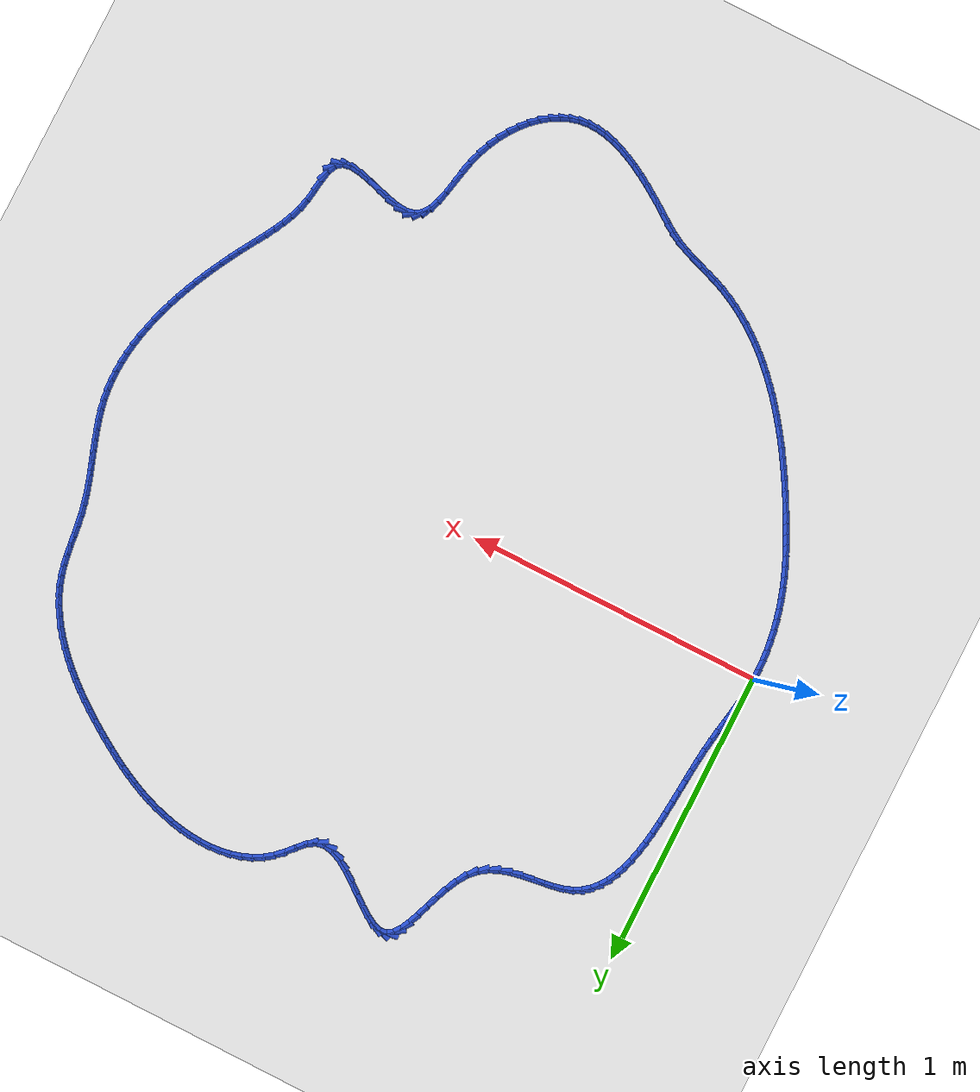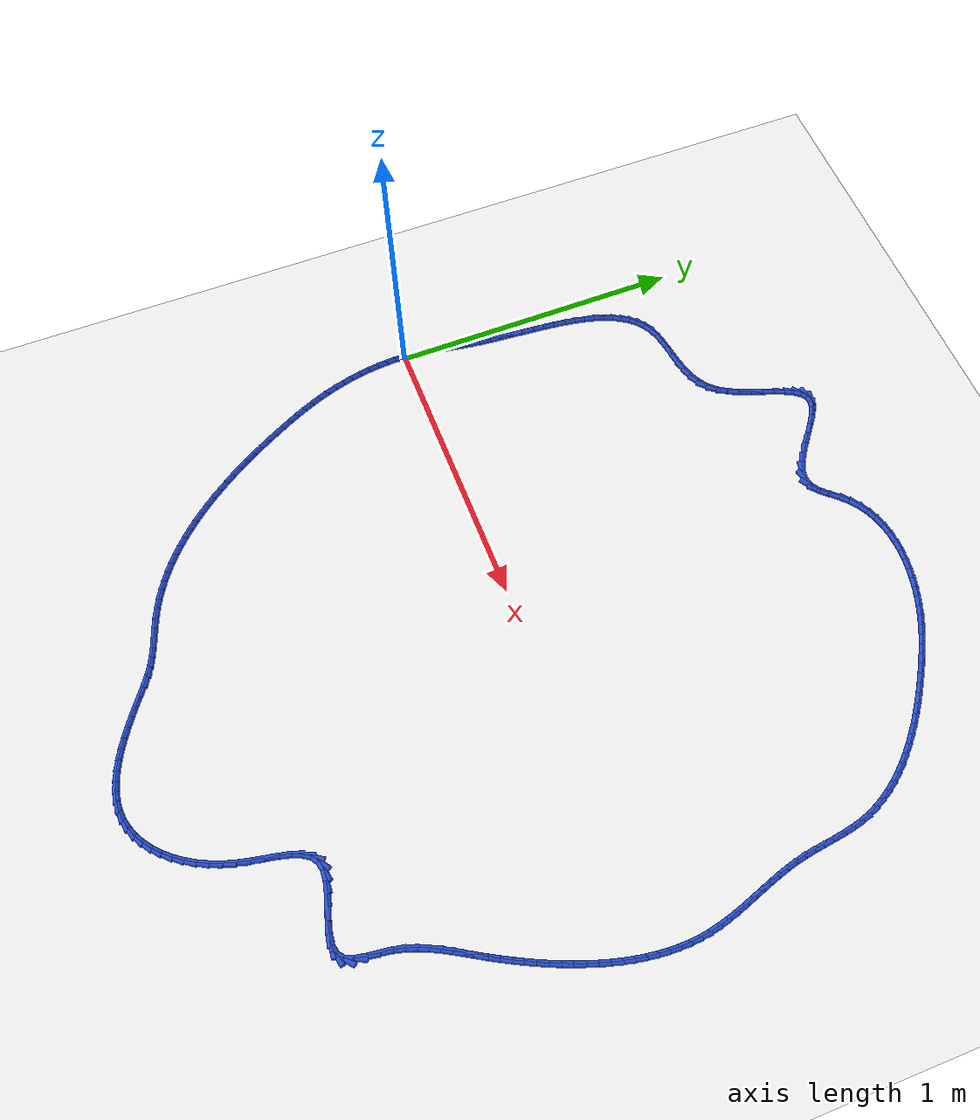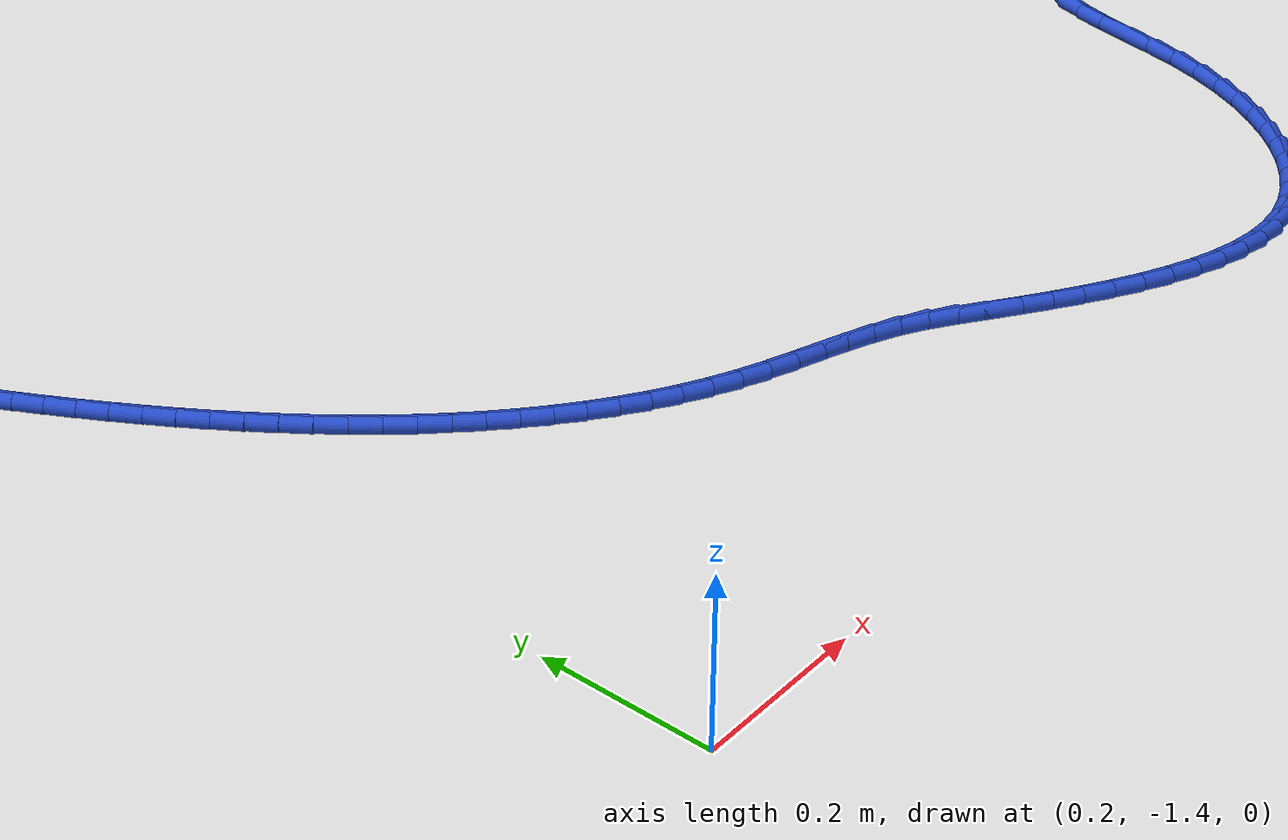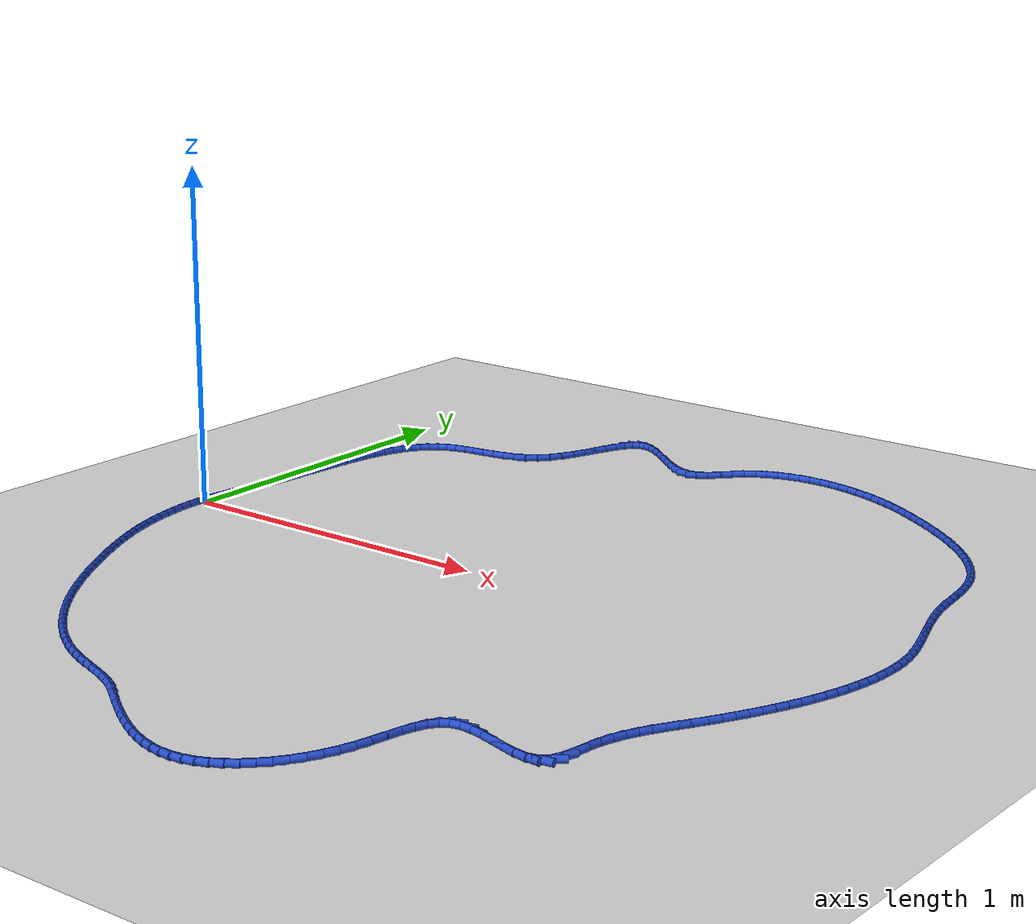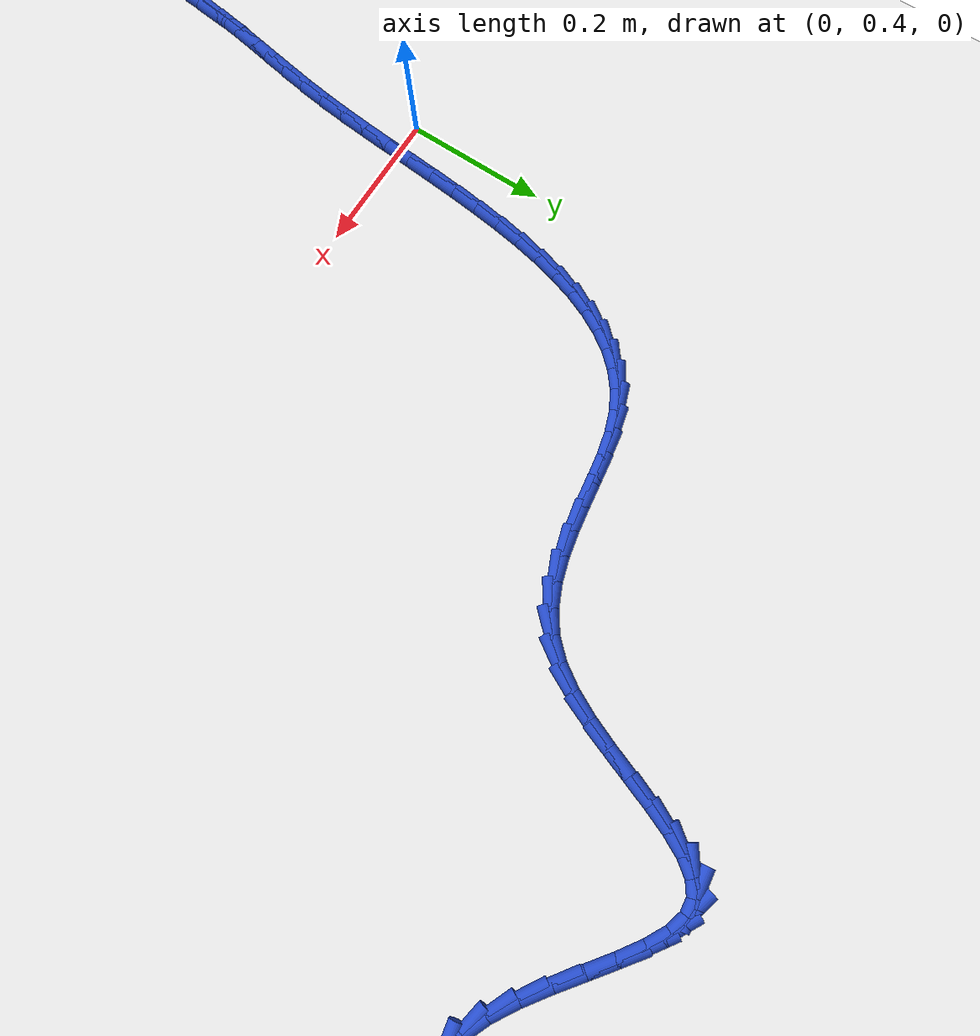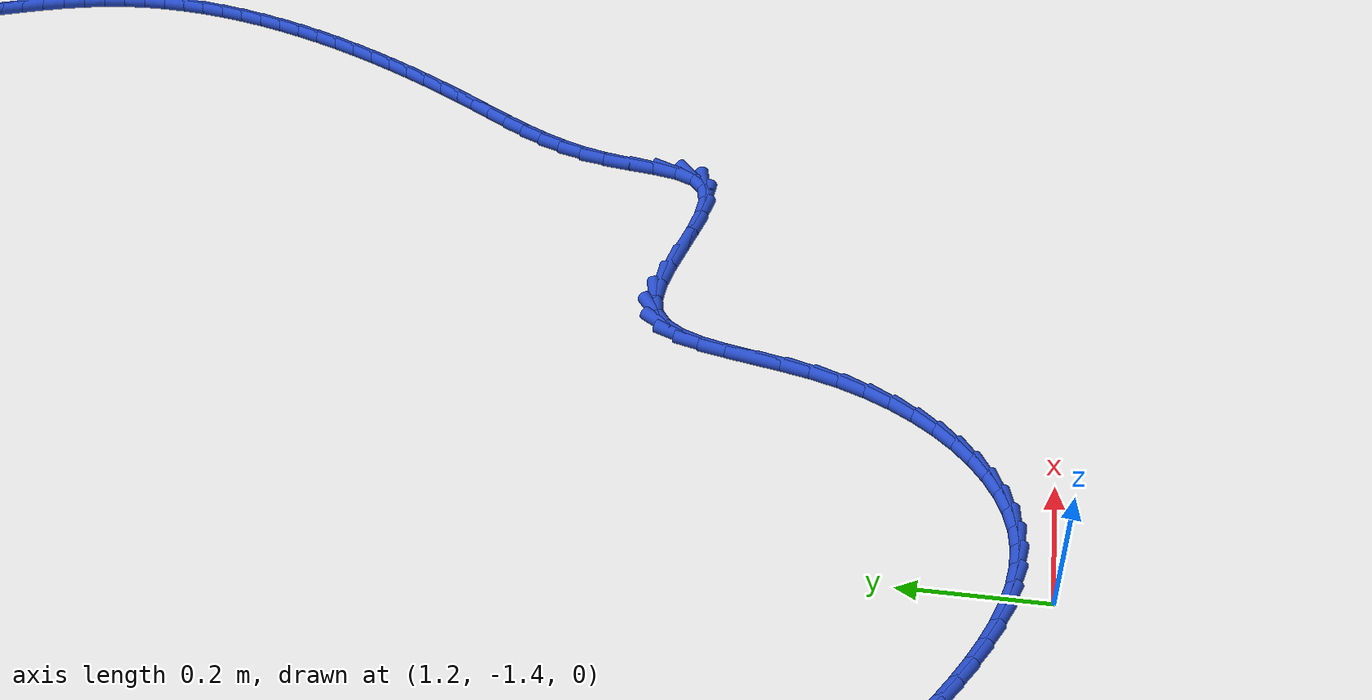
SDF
<sdf version="1.6">
 <world name="default">
  <light name="sun" type="directional">
   <pose>0 0 10 0 -0 0</pose>
   <diffuse>0.8 0.8 0.8 1</diffuse>
   <specular>0.2 0.2 0.2 1</specular>
   <attenuation>
    <range>1000</range>
    <constant>0.9</constant>
    <linear>0.01</linear>
    <quadratic>0.001</quadratic>
   </attenuation>
   <direction>-0.5 0.1 -0.9</direction>
  </light>
  <model name="ground_plane">
   <static>1</static>
   <link name="link">
    <collision name="collision">
     <geometry><plane><normal>0 0 1</normal><size>100 100</size></plane></geometry>
     <surface><friction><ode><mu>100</mu><mu2>50</mu2></ode></friction></surface>
    </collision>
    <visual name="visual">
     <cast_shadows>0</cast_shadows>
     <geometry><plane><normal>0 0 1</normal><size>100 100</size></plane></geometry>
     <material>
      <script><uri>file://media/materials/scripts/gazebo.material</uri><name>Gazebo/WhiteGlow</name></script>
     </material>
    </visual>
   </link>
  </model>
  <gravity>0 0 -9.8</gravity>
  <magnetic_field>6e-06 2.3e-05 -4.2e-05</magnetic_field>
  <atmosphere type="adiabatic"/>
  <physics name="default_physics" default="0" type="ode">
   <max_step_size>0.001</max_step_size>
   <real_time_factor>1</real_time_factor>
   <real_time_update_rate>1000</real_time_update_rate>
  </physics>
  <scene><ambient>0.4 0.4 0.4 1</ambient><background>0.7 0.7 0.7 1</background><shadows>1</shadows></scene>
  <spherical_coordinates>
   <surface_model>EARTH_WGS84</surface_model>
   <latitude_deg>0</latitude_deg>
   <longitude_deg>0</longitude_deg>
   <elevation>0</elevation>
   <heading_deg>0</heading_deg>
  </spherical_coordinates>
  <model name="line">
   <link name="link_0">
    <pose>-8.673617379884035e-18 6.938893903907228e-17 0.01 0 1.57 1.5066967162168163</pose>
    <collision name="collision">
     <geometry><cylinder><radius>0.01</radius><length>0.08</length></cylinder></geometry>
    </collision>
    <visual name="visual">
     <material>
      <script><name>Gazebo/Blue</name><uri>file://media/materials/scripts/gazebo.material</uri></script>
     </material>
     <geometry><cylinder><radius>0.01</radius><length>0.08</length></cylinder></geometry>
    </visual>
   </link>
   <link name="link_1">
    <pose>0.0021181795967309134 0.0329998536982295 0.01 0 1.57 1.4651399813754398</pose>
    <collision name="collision">
     <geometry><cylinder><radius>0.01</radius><length>0.08</length></cylinder></geometry>
    </collision>
    <visual name="visual">
     <material>
      <script><name>Gazebo/Blue</name><uri>file://media/materials/scripts/gazebo.material</uri></script>
     </material>
     <geometry><cylinder><radius>0.01</radius><length>0.08</length></cylinder></geometry>
    </visual>
   </link>
   <link name="link_2">
    <pose>0.005590243179879086 0.06573933650585143 0.01 0 1.57 1.4338351481896856</pose>
    <collision name="collision">
     <geometry><cylinder><radius>0.01</radius><length>0.08</length></cylinder></geometry>
    </collision>
    <visual name="visual">
     <material>
      <script><name>Gazebo/Blue</name><uri>file://media/materials/scripts/gazebo.material</uri></script>
     </material>
     <geometry><cylinder><radius>0.01</radius><length>0.08</length></cylinder></geometry>
    </visual>
   </link>
   <link name="link_3">
    <pose>0.010098710320919392 0.09845109745758833 0.01 0 1.57 1.4133048050352077</pose>
    <collision name="collision">
     <geometry><cylinder><radius>0.01</radius><length>0.08</length></cylinder></geometry>
    </collision>
    <visual name="visual">
     <material>
      <script><name>Gazebo/Blue</name><uri>file://media/materials/scripts/gazebo.material</uri></script>
     </material>
     <geometry><cylinder><radius>0.01</radius><length>0.08</length></cylinder></geometry>
    </visual>
   </link>
   <link name="link_4">
    <pose>0.015326100591326686 0.1313677855881625 0.01 0 1.57 1.4036125392366483</pose>
    <collision name="collision">
     <geometry><cylinder><radius>0.01</radius><length>0.08</length></cylinder></geometry>
    </collision>
    <visual name="visual">
     <material>
      <script><name>Gazebo/Blue</name><uri>file://media/materials/scripts/gazebo.material</uri></script>
     </material>
     <geometry><cylinder><radius>0.01</radius><length>0.08</length></cylinder></geometry>
    </visual>
   </link>
   <link name="link_5">
    <pose>0.020954933562575835 0.16472204993229628 0.01 0 1.57 1.4044455047664022</pose>
    <collision name="collision">
     <geometry><cylinder><radius>0.01</radius><length>0.08</length></cylinder></geometry>
    </collision>
    <visual name="visual">
     <material>
      <script><name>Gazebo/Blue</name><uri>file://media/materials/scripts/gazebo.material</uri></script>
     </material>
     <geometry><cylinder><radius>0.01</radius><length>0.08</length></cylinder></geometry>
    </visual>
   </link>
   <link name="link_6">
    <pose>0.02666772880614173 0.19874653952471222 0.01 0 1.57 1.4151882282810488</pose>
    <collision name="collision">
     <geometry><cylinder><radius>0.01</radius><length>0.08</length></cylinder></geometry>
    </collision>
    <visual name="visual">
     <material>
      <script><name>Gazebo/Blue</name><uri>file://media/materials/scripts/gazebo.material</uri></script>
     </material>
     <geometry><cylinder><radius>0.01</radius><length>0.08</length></cylinder></geometry>
    </visual>
   </link>
   <link name="link_7">
    <pose>0.032147005893499205 0.23367390340013242 0.01 0 1.57 1.4349797305849115</pose>
    <collision name="collision">
     <geometry><cylinder><radius>0.01</radius><length>0.08</length></cylinder></geometry>
    </collision>
    <visual name="visual">
     <material>
      <script><name>Gazebo/Blue</name><uri>file://media/materials/scripts/gazebo.material</uri></script>
     </material>
     <geometry><cylinder><radius>0.01</radius><length>0.08</length></cylinder></geometry>
    </visual>
   </link>
   <link name="link_8">
    <pose>0.03707528439612314 0.2697367905932794 0.01 0 1.57 1.4600571389760253</pose>
    <collision name="collision">
     <geometry><cylinder><radius>0.01</radius><length>0.08</length></cylinder></geometry>
    </collision>
    <visual name="visual">
     <material>
      <script><name>Gazebo/Blue</name><uri>file://media/materials/scripts/gazebo.material</uri></script>
     </material>
     <geometry><cylinder><radius>0.01</radius><length>0.08</length></cylinder></geometry>
    </visual>
   </link>
   <link name="link_9">
    <pose>0.041227540492026836 0.3070792076161011 0.01 0 1.57 1.47933426836832</pose>
    <collision name="collision">
     <geometry><cylinder><radius>0.01</radius><length>0.08</length></cylinder></geometry>
    </collision>
    <visual name="visual">
     <material>
      <script><name>Gazebo/Blue</name><uri>file://media/materials/scripts/gazebo.material</uri></script>
     </material>
     <geometry><cylinder><radius>0.01</radius><length>0.08</length></cylinder></geometry>
    </visual>
   </link>
   <link name="link_10">
    <pose>0.04475039405332357 0.3454888485886928 0.01 0 1.57 1.4909806740862932</pose>
    <collision name="collision">
     <geometry><cylinder><radius>0.01</radius><length>0.08</length></cylinder></geometry>
    </collision>
    <visual name="visual">
     <material>
      <script><name>Gazebo/Blue</name><uri>file://media/materials/scripts/gazebo.material</uri></script>
     </material>
     <geometry><cylinder><radius>0.01</radius><length>0.08</length></cylinder></geometry>
    </visual>
   </link>
   <link name="link_11">
    <pose>0.04788383242284773 0.3846638918197912 0.01 0 1.57 1.4956576767791538</pose>
    <collision name="collision">
     <geometry><cylinder><radius>0.01</radius><length>0.08</length></cylinder></geometry>
    </collision>
    <visual name="visual">
     <material>
      <script><name>Gazebo/Blue</name><uri>file://media/materials/scripts/gazebo.material</uri></script>
     </material>
     <geometry><cylinder><radius>0.01</radius><length>0.08</length></cylinder></geometry>
    </visual>
   </link>
   <link name="link_12">
    <pose>0.050867842943838955 0.42430251561774424 0.01 0 1.57 1.493699682080578</pose>
    <collision name="collision">
     <geometry><cylinder><radius>0.01</radius><length>0.08</length></cylinder></geometry>
    </collision>
    <visual name="visual">
     <material>
      <script><name>Gazebo/Blue</name><uri>file://media/materials/scripts/gazebo.material</uri></script>
     </material>
     <geometry><cylinder><radius>0.01</radius><length>0.08</length></cylinder></geometry>
    </visual>
   </link>
   <link name="link_13">
    <pose>0.05394241295953693 0.4641028982908998 0.01 0 1.57 1.4851493421027155</pose>
    <collision name="collision">
     <geometry><cylinder><radius>0.01</radius><length>0.08</length></cylinder></geometry>
    </collision>
    <visual name="visual">
     <material>
      <script><name>Gazebo/Blue</name><uri>file://media/materials/scripts/gazebo.material</uri></script>
     </material>
     <geometry><cylinder><radius>0.01</radius><length>0.08</length></cylinder></geometry>
    </visual>
   </link>
   <link name="link_14">
    <pose>0.05734752981318129 0.5037632181476058 0.01 0 1.57 1.469769448681049</pose>
    <collision name="collision">
     <geometry><cylinder><radius>0.01</radius><length>0.08</length></cylinder></geometry>
    </collision>
    <visual name="visual">
     <material>
      <script><name>Gazebo/Blue</name><uri>file://media/materials/scripts/gazebo.material</uri></script>
     </material>
     <geometry><cylinder><radius>0.01</radius><length>0.08</length></cylinder></geometry>
    </visual>
   </link>
   <link name="link_15">
    <pose>0.061323180848011694 0.5429816534962103 0.01 0 1.57 1.4470342885404268</pose>
    <collision name="collision">
     <geometry><cylinder><radius>0.01</radius><length>0.08</length></cylinder></geometry>
    </collision>
    <visual name="visual">
     <material>
      <script><name>Gazebo/Blue</name><uri>file://media/materials/scripts/gazebo.material</uri></script>
     </material>
     <geometry><cylinder><radius>0.01</radius><length>0.08</length></cylinder></geometry>
    </visual>
   </link>
   <link name="link_16">
    <pose>0.06610935340726783 0.5814563826450613 0.01 0 1.57 1.4161029471662532</pose>
    <collision name="collision">
     <geometry><cylinder><radius>0.01</radius><length>0.08</length></cylinder></geometry>
    </collision>
    <visual name="visual">
     <material>
      <script><name>Gazebo/Blue</name><uri>file://media/materials/scripts/gazebo.material</uri></script>
     </material>
     <geometry><cylinder><radius>0.01</radius><length>0.08</length></cylinder></geometry>
    </visual>
   </link>
   <link name="link_17">
    <pose>0.07194603483418932 0.6188855839025065 0.01 0 1.57 1.3757787722762227</pose>
    <collision name="collision">
     <geometry><cylinder><radius>0.01</radius><length>0.08</length></cylinder></geometry>
    </collision>
    <visual name="visual">
     <material>
      <script><name>Gazebo/Blue</name><uri>file://media/materials/scripts/gazebo.material</uri></script>
     </material>
     <geometry><cylinder><radius>0.01</radius><length>0.08</length></cylinder></geometry>
    </visual>
   </link>
   <link name="link_18">
    <pose>0.07907321247201582 0.6549674355768937 0.01 0 1.57 1.3244653415523293</pose>
    <collision name="collision">
     <geometry><cylinder><radius>0.01</radius><length>0.08</length></cylinder></geometry>
    </collision>
    <visual name="visual">
     <material>
      <script><name>Gazebo/Blue</name><uri>file://media/materials/scripts/gazebo.material</uri></script>
     </material>
     <geometry><cylinder><radius>0.01</radius><length>0.08</length></cylinder></geometry>
    </visual>
   </link>
   <link name="link_19">
    <pose>0.08773087366398699 0.6894001159765711 0.01 0 1.57 1.2601443776748615</pose>
    <collision name="collision">
     <geometry><cylinder><radius>0.01</radius><length>0.08</length></cylinder></geometry>
    </collision>
    <visual name="visual">
     <material>
      <script><name>Gazebo/Blue</name><uri>file://media/materials/scripts/gazebo.material</uri></script>
     </material>
     <geometry><cylinder><radius>0.01</radius><length>0.08</length></cylinder></geometry>
    </visual>
   </link>
   <link name="link_20">
    <pose>0.09815900575334251 0.7218818034098867 0.01 0 1.57 1.1804323501548057</pose>
    <collision name="collision">
     <geometry><cylinder><radius>0.01</radius><length>0.08</length></cylinder></geometry>
    </collision>
    <visual name="visual">
     <material>
      <script><name>Gazebo/Blue</name><uri>file://media/materials/scripts/gazebo.material</uri></script>
     </material>
     <geometry><cylinder><radius>0.01</radius><length>0.08</length></cylinder></geometry>
    </visual>
   </link>
   <link name="link_21">
    <pose>0.11059759608332205 0.7521106761851886 0.01 0 1.57 1.0828260451746954</pose>
    <collision name="collision">
     <geometry><cylinder><radius>0.01</radius><length>0.08</length></cylinder></geometry>
    </collision>
    <visual name="visual">
     <material>
      <script><name>Gazebo/Blue</name><uri>file://media/materials/scripts/gazebo.material</uri></script>
     </material>
     <geometry><cylinder><radius>0.01</radius><length>0.08</length></cylinder></geometry>
    </visual>
   </link>
   <link name="link_22">
    <pose>0.1252866319971652 0.779784912610824 0.01 0 1.57 0.9653080502679429</pose>
    <collision name="collision">
     <geometry><cylinder><radius>0.01</radius><length>0.08</length></cylinder></geometry>
    </collision>
    <visual name="visual">
     <material>
      <script><name>Gazebo/Blue</name><uri>file://media/materials/scripts/gazebo.material</uri></script>
     </material>
     <geometry><cylinder><radius>0.01</radius><length>0.08</length></cylinder></geometry>
    </visual>
   </link>
   <link name="link_23">
    <pose>0.1424661008381117 0.8046026909951417 0.01 0 1.57 0.8274622302756662</pose>
    <collision name="collision">
     <geometry><cylinder><radius>0.01</radius><length>0.08</length></cylinder></geometry>
    </collision>
    <visual name="visual">
     <material>
      <script><name>Gazebo/Blue</name><uri>file://media/materials/scripts/gazebo.material</uri></script>
     </material>
     <geometry><cylinder><radius>0.01</radius><length>0.08</length></cylinder></geometry>
    </visual>
   </link>
   <link name="link_24">
    <pose>0.16237598994940114 0.826262189646489 0.01 0 1.57 0.6719407179027711</pose>
    <collision name="collision">
     <geometry><cylinder><radius>0.01</radius><length>0.08</length></cylinder></geometry>
    </collision>
    <visual name="visual">
     <material>
      <script><name>Gazebo/Blue</name><uri>file://media/materials/scripts/gazebo.material</uri></script>
     </material>
     <geometry><cylinder><radius>0.01</radius><length>0.08</length></cylinder></geometry>
    </visual>
   </link>
   <link name="link_25">
    <pose>0.18525628667427319 0.8444615868732144 0.01 0 1.57 0.5054171204110706</pose>
    <collision name="collision">
     <geometry><cylinder><radius>0.01</radius><length>0.08</length></cylinder></geometry>
    </collision>
    <visual name="visual">
     <material>
      <script><name>Gazebo/Blue</name><uri>file://media/materials/scripts/gazebo.material</uri></script>
     </material>
     <geometry><cylinder><radius>0.01</radius><length>0.08</length></cylinder></geometry>
    </visual>
   </link>
   <link name="link_26">
    <pose>0.21134697835596758 0.8588990609836653 0.01 0 1.57 0.3440407389144049</pose>
    <collision name="collision">
     <geometry><cylinder><radius>0.01</radius><length>0.08</length></cylinder></geometry>
    </collision>
    <visual name="visual">
     <material>
      <script><name>Gazebo/Blue</name><uri>file://media/materials/scripts/gazebo.material</uri></script>
     </material>
     <geometry><cylinder><radius>0.01</radius><length>0.08</length></cylinder></geometry>
    </visual>
   </link>
   <link name="link_27">
    <pose>0.2407686229127443 0.869440535133381 0.01 0 1.57 0.2285616109547819</pose>
    <collision name="collision">
     <geometry><cylinder><radius>0.01</radius><length>0.08</length></cylinder></geometry>
    </collision>
    <visual name="visual">
     <material>
      <script><name>Gazebo/Blue</name><uri>file://media/materials/scripts/gazebo.material</uri></script>
     </material>
     <geometry><cylinder><radius>0.01</radius><length>0.08</length></cylinder></geometry>
    </visual>
   </link>
   <link name="link_28">
    <pose>0.27294803977817456 0.8769263243090983 0.01 0 1.57 0.16331307696092154</pose>
    <collision name="collision">
     <geometry><cylinder><radius>0.01</radius><length>0.08</length></cylinder></geometry>
    </collision>
    <visual name="visual">
     <material>
      <script><name>Gazebo/Blue</name><uri>file://media/materials/scripts/gazebo.material</uri></script>
     </material>
     <geometry><cylinder><radius>0.01</radius><length>0.08</length></cylinder></geometry>
    </visual>
   </link>
   <link name="link_29">
    <pose>0.3070621940663292 0.882547676901544 0.01 0 1.57 0.13957083259724673</pose>
    <collision name="collision">
     <geometry><cylinder><radius>0.01</radius><length>0.08</length></cylinder></geometry>
    </collision>
    <visual name="visual">
     <material>
      <script><name>Gazebo/Blue</name><uri>file://media/materials/scripts/gazebo.material</uri></script>
     </material>
     <geometry><cylinder><radius>0.01</radius><length>0.08</length></cylinder></geometry>
    </visual>
   </link>
   <link name="link_30">
    <pose>0.3422877188505929 0.8874963076698804 0.01 0 1.57 0.1527594642650867</pose>
    <collision name="collision">
     <geometry><cylinder><radius>0.01</radius><length>0.08</length></cylinder></geometry>
    </collision>
    <visual name="visual">
     <material>
      <script><name>Gazebo/Blue</name><uri>file://media/materials/scripts/gazebo.material</uri></script>
     </material>
     <geometry><cylinder><radius>0.01</radius><length>0.08</length></cylinder></geometry>
    </visual>
   </link>
   <link name="link_31">
    <pose>0.3778012472043501 0.8929639313732707 0.01 0 1.57 0.20241279804955686</pose>
    <collision name="collision">
     <geometry><cylinder><radius>0.01</radius><length>0.08</length></cylinder></geometry>
    </collision>
    <visual name="visual">
     <material>
      <script><name>Gazebo/Blue</name><uri>file://media/materials/scripts/gazebo.material</uri></script>
     </material>
     <geometry><cylinder><radius>0.01</radius><length>0.08</length></cylinder></geometry>
    </visual>
   </link>
   <link name="link_32">
    <pose>0.4127794122009857 0.9001422627708784 0.01 0 1.57 0.2913182558403613</pose>
    <collision name="collision">
     <geometry><cylinder><radius>0.01</radius><length>0.08</length></cylinder></geometry>
    </collision>
    <visual name="visual">
     <material>
      <script><name>Gazebo/Blue</name><uri>file://media/materials/scripts/gazebo.material</uri></script>
     </material>
     <geometry><cylinder><radius>0.01</radius><length>0.08</length></cylinder></geometry>
    </visual>
   </link>
   <link name="link_33">
    <pose>0.4463988469138838 0.9102230166218654 0.01 0 1.57 0.4235967110291509</pose>
    <collision name="collision">
     <geometry><cylinder><radius>0.01</radius><length>0.08</length></cylinder></geometry>
    </collision>
    <visual name="visual">
     <material>
      <script><name>Gazebo/Blue</name><uri>file://media/materials/scripts/gazebo.material</uri></script>
     </material>
     <geometry><cylinder><radius>0.01</radius><length>0.08</length></cylinder></geometry>
    </visual>
   </link>
   <link name="link_34">
    <pose>0.47783618441642933 0.9243979076853951 0.01 0 1.57 0.6002264170728235</pose>
    <collision name="collision">
     <geometry><cylinder><radius>0.01</radius><length>0.08</length></cylinder></geometry>
    </collision>
    <visual name="visual">
     <material>
      <script><name>Gazebo/Blue</name><uri>file://media/materials/scripts/gazebo.material</uri></script>
     </material>
     <geometry><cylinder><radius>0.01</radius><length>0.08</length></cylinder></geometry>
    </visual>
   </link>
   <link name="link_35">
    <pose>0.5062680577820068 0.9438586507206308 0.01 0 1.57 0.8090391086718112</pose>
    <collision name="collision">
     <geometry><cylinder><radius>0.01</radius><length>0.08</length></cylinder></geometry>
    </collision>
    <visual name="visual">
     <material>
      <script><name>Gazebo/Blue</name><uri>file://media/materials/scripts/gazebo.material</uri></script>
     </material>
     <geometry><cylinder><radius>0.01</radius><length>0.08</length></cylinder></geometry>
    </visual>
   </link>
   <link name="link_36">
    <pose>0.5309199760902127 0.969704609021901 0.01 0 1.57 0.9880619966832562</pose>
    <collision name="collision">
     <geometry><cylinder><radius>0.01</radius><length>0.08</length></cylinder></geometry>
    </collision>
    <visual name="visual">
     <material>
      <script><name>Gazebo/Blue</name><uri>file://media/materials/scripts/gazebo.material</uri></script>
     </material>
     <geometry><cylinder><radius>0.01</radius><length>0.08</length></cylinder></geometry>
    </visual>
   </link>
   <link name="link_37">
    <pose>0.5518503437649304 1.001461385851583 0.01 0 1.57 1.106547656888992</pose>
    <collision name="collision">
     <geometry><cylinder><radius>0.01</radius><length>0.08</length></cylinder></geometry>
    </collision>
    <visual name="visual">
     <material>
      <script><name>Gazebo/Blue</name><uri>file://media/materials/scripts/gazebo.material</uri></script>
     </material>
     <geometry><cylinder><radius>0.01</radius><length>0.08</length></cylinder></geometry>
    </visual>
   </link>
   <link name="link_38">
    <pose>0.56981500103304 1.0373367759392773 0.01 0 1.57 1.1787809687492365</pose>
    <collision name="collision">
     <geometry><cylinder><radius>0.01</radius><length>0.08</length></cylinder></geometry>
    </collision>
    <visual name="visual">
     <material>
      <script><name>Gazebo/Blue</name><uri>file://media/materials/scripts/gazebo.material</uri></script>
     </material>
     <geometry><cylinder><radius>0.01</radius><length>0.08</length></cylinder></geometry>
    </visual>
   </link>
   <link name="link_39">
    <pose>0.5855913043726308 1.0754979189473892 0.01 0 1.57 1.2146382591876208</pose>
    <collision name="collision">
     <geometry><cylinder><radius>0.01</radius><length>0.08</length></cylinder></geometry>
    </collision>
    <visual name="visual">
     <material>
      <script><name>Gazebo/Blue</name><uri>file://media/materials/scripts/gazebo.material</uri></script>
     </material>
     <geometry><cylinder><radius>0.01</radius><length>0.08</length></cylinder></geometry>
    </visual>
   </link>
   <link name="link_40">
    <pose>0.5999566102617917 1.1141119545383242 0.01 0 1.57 1.217478451750848</pose>
    <collision name="collision">
     <geometry><cylinder><radius>0.01</radius><length>0.08</length></cylinder></geometry>
    </collision>
    <visual name="visual">
     <material>
      <script><name>Gazebo/Blue</name><uri>file://media/materials/scripts/gazebo.material</uri></script>
     </material>
     <geometry><cylinder><radius>0.01</radius><length>0.08</length></cylinder></geometry>
    </visual>
   </link>
   <link name="link_41">
    <pose>0.6136882751786112 1.1513460223744874 0.01 0 1.57 1.1835456714124042</pose>
    <collision name="collision">
     <geometry><cylinder><radius>0.01</radius><length>0.08</length></cylinder></geometry>
    </collision>
    <visual name="visual">
     <material>
      <script><name>Gazebo/Blue</name><uri>file://media/materials/scripts/gazebo.material</uri></script>
     </material>
     <geometry><cylinder><radius>0.01</radius><length>0.08</length></cylinder></geometry>
    </visual>
   </link>
   <link name="link_42">
    <pose>0.6275636556011782 1.1853672621182834 0.01 0 1.57 1.0986626775487782</pose>
    <collision name="collision">
     <geometry><cylinder><radius>0.01</radius><length>0.08</length></cylinder></geometry>
    </collision>
    <visual name="visual">
     <material>
      <script><name>Gazebo/Blue</name><uri>file://media/materials/scripts/gazebo.material</uri></script>
     </material>
     <geometry><cylinder><radius>0.01</radius><length>0.08</length></cylinder></geometry>
    </visual>
   </link>
   <link name="link_43">
    <pose>0.6423601080075816 1.2143428134321175 0.01 0 1.57 0.9295544306102976</pose>
    <collision name="collision">
     <geometry><cylinder><radius>0.01</radius><length>0.08</length></cylinder></geometry>
    </collision>
    <visual name="visual">
     <material>
      <script><name>Gazebo/Blue</name><uri>file://media/materials/scripts/gazebo.material</uri></script>
     </material>
     <geometry><cylinder><radius>0.01</radius><length>0.08</length></cylinder></geometry>
    </visual>
   </link>
   <link name="link_44">
    <pose>0.6588549888759102 1.2364398159783954 0.01 0 1.57 0.6144706610278099</pose>
    <collision name="collision">
     <geometry><cylinder><radius>0.01</radius><length>0.08</length></cylinder></geometry>
    </collision>
    <visual name="visual">
     <material>
      <script><name>Gazebo/Blue</name><uri>file://media/materials/scripts/gazebo.material</uri></script>
     </material>
     <geometry><cylinder><radius>0.01</radius><length>0.08</length></cylinder></geometry>
    </visual>
   </link>
   <link name="link_45">
    <pose>0.6778256546842527 1.2498254094195214 0.01 0 1.57 0.12982233505834545</pose>
    <collision name="collision">
     <geometry><cylinder><radius>0.01</radius><length>0.08</length></cylinder></geometry>
    </collision>
    <visual name="visual">
     <material>
      <script><name>Gazebo/Blue</name><uri>file://media/materials/scripts/gazebo.material</uri></script>
     </material>
     <geometry><cylinder><radius>0.01</radius><length>0.08</length></cylinder></geometry>
    </visual>
   </link>
   <link name="link_46">
    <pose>0.7000303085403444 1.2527243739877905 0.01 0 1.57 -0.2857190893415801</pose>
    <collision name="collision">
     <geometry><cylinder><radius>0.01</radius><length>0.08</length></cylinder></geometry>
    </collision>
    <visual name="visual">
     <material>
      <script><name>Gazebo/Blue</name><uri>file://media/materials/scripts/gazebo.material</uri></script>
     </material>
     <geometry><cylinder><radius>0.01</radius><length>0.08</length></cylinder></geometry>
    </visual>
   </link>
   <link name="link_47">
    <pose>0.7256131645809981 1.2452092416968248 0.01 0 1.57 -0.5043320786215698</pose>
    <collision name="collision">
     <geometry><cylinder><radius>0.01</radius><length>0.08</length></cylinder></geometry>
    </collision>
    <visual name="visual">
     <material>
      <script><name>Gazebo/Blue</name><uri>file://media/materials/scripts/gazebo.material</uri></script>
     </material>
     <geometry><cylinder><radius>0.01</radius><length>0.08</length></cylinder></geometry>
    </visual>
   </link>
   <link name="link_48">
    <pose>0.7539891093596383 1.2295473988739276 0.01 0 1.57 -0.6114819625548455</pose>
    <collision name="collision">
     <geometry><cylinder><radius>0.01</radius><length>0.08</length></cylinder></geometry>
    </collision>
    <visual name="visual">
     <material>
      <script><name>Gazebo/Blue</name><uri>file://media/materials/scripts/gazebo.material</uri></script>
     </material>
     <geometry><cylinder><radius>0.01</radius><length>0.08</length></cylinder></geometry>
    </visual>
   </link>
   <link name="link_49">
    <pose>0.7845305938335502 1.2081339384536351 0.01 0 1.57 -0.6575235081321753</pose>
    <collision name="collision">
     <geometry><cylinder><radius>0.01</radius><length>0.08</length></cylinder></geometry>
    </collision>
    <visual name="visual">
     <material>
      <script><name>Gazebo/Blue</name><uri>file://media/materials/scripts/gazebo.material</uri></script>
     </material>
     <geometry><cylinder><radius>0.01</radius><length>0.08</length></cylinder></geometry>
    </visual>
   </link>
   <link name="link_50">
    <pose>0.81661006896002 1.1833639533704845 0.01 0 1.57 -0.6624127575131042</pose>
    <collision name="collision">
     <geometry><cylinder><radius>0.01</radius><length>0.08</length></cylinder></geometry>
    </collision>
    <visual name="visual">
     <material>
      <script><name>Gazebo/Blue</name><uri>file://media/materials/scripts/gazebo.material</uri></script>
     </material>
     <geometry><cylinder><radius>0.01</radius><length>0.08</length></cylinder></geometry>
    </visual>
   </link>
   <link name="link_51">
    <pose>0.8495999856963333 1.157632536559012 0.01 0 1.57 -0.6307464454100689</pose>
    <collision name="collision">
     <geometry><cylinder><radius>0.01</radius><length>0.08</length></cylinder></geometry>
    </collision>
    <visual name="visual">
     <material>
      <script><name>Gazebo/Blue</name><uri>file://media/materials/scripts/gazebo.material</uri></script>
     </material>
     <geometry><cylinder><radius>0.01</radius><length>0.08</length></cylinder></geometry>
    </visual>
   </link>
   <link name="link_52">
    <pose>0.8828727949997763 1.1333347809537553 0.01 0 1.57 -0.5561695094122968</pose>
    <collision name="collision">
     <geometry><cylinder><radius>0.01</radius><length>0.08</length></cylinder></geometry>
    </collision>
    <visual name="visual">
     <material>
      <script><name>Gazebo/Blue</name><uri>file://media/materials/scripts/gazebo.material</uri></script>
     </material>
     <geometry><cylinder><radius>0.01</radius><length>0.08</length></cylinder></geometry>
    </visual>
   </link>
   <link name="link_53">
    <pose>0.9158009478276345 1.1128657794892507 0.01 0 1.57 -0.4193346537623533</pose>
    <collision name="collision">
     <geometry><cylinder><radius>0.01</radius><length>0.08</length></cylinder></geometry>
    </collision>
    <visual name="visual">
     <material>
      <script><name>Gazebo/Blue</name><uri>file://media/materials/scripts/gazebo.material</uri></script>
     </material>
     <geometry><cylinder><radius>0.01</radius><length>0.08</length></cylinder></geometry>
    </visual>
   </link>
   <link name="link_54">
    <pose>0.9477568951371937 1.0986206251000354 0.01 0 1.57 -0.1832604188640608</pose>
    <collision name="collision">
     <geometry><cylinder><radius>0.01</radius><length>0.08</length></cylinder></geometry>
    </collision>
    <visual name="visual">
     <material>
      <script><name>Gazebo/Blue</name><uri>file://media/materials/scripts/gazebo.material</uri></script>
     </material>
     <geometry><cylinder><radius>0.01</radius><length>0.08</length></cylinder></geometry>
    </visual>
   </link>
   <link name="link_55">
    <pose>0.9781130878857398 1.092994410720646 0.01 0 1.57 0.18881475932484434</pose>
    <collision name="collision">
     <geometry><cylinder><radius>0.01</radius><length>0.08</length></cylinder></geometry>
    </collision>
    <visual name="visual">
     <material>
      <script><name>Gazebo/Blue</name><uri>file://media/materials/scripts/gazebo.material</uri></script>
     </material>
     <geometry><cylinder><radius>0.01</radius><length>0.08</length></cylinder></geometry>
    </visual>
   </link>
   <link name="link_56">
    <pose>1.0062453580594475 1.0983702354294929 0.01 0 1.57 0.5744482949221402</pose>
    <collision name="collision">
     <geometry><cylinder><radius>0.01</radius><length>0.08</length></cylinder></geometry>
    </collision>
    <visual name="visual">
     <material>
      <script><name>Gazebo/Blue</name><uri>file://media/materials/scripts/gazebo.material</uri></script>
     </material>
     <geometry><cylinder><radius>0.01</radius><length>0.08</length></cylinder></geometry>
    </visual>
   </link>
   <link name="link_57">
    <pose>1.0321006123909109 1.1151053687214427 0.01 0 1.57 0.7737076027221083</pose>
    <collision name="collision">
     <geometry><cylinder><radius>0.01</radius><length>0.08</length></cylinder></geometry>
    </collision>
    <visual name="visual">
     <material>
      <script><name>Gazebo/Blue</name><uri>file://media/materials/scripts/gazebo.material</uri></script>
     </material>
     <geometry><cylinder><radius>0.01</radius><length>0.08</length></cylinder></geometry>
    </visual>
   </link>
   <link name="link_58">
    <pose>1.056834849722386 1.1392679487992778 0.01 0 1.57 0.8274370004401611</pose>
    <collision name="collision">
     <geometry><cylinder><radius>0.01</radius><length>0.08</length></cylinder></geometry>
    </collision>
    <visual name="visual">
     <material>
      <script><name>Gazebo/Blue</name><uri>file://media/materials/scripts/gazebo.material</uri></script>
     </material>
     <geometry><cylinder><radius>0.01</radius><length>0.08</length></cylinder></geometry>
    </visual>
   </link>
   <link name="link_59">
    <pose>1.0817580379433256 1.1663799243298014 0.01 0 1.57 0.7698169462939558</pose>
    <collision name="collision">
     <geometry><cylinder><radius>0.01</radius><length>0.08</length></cylinder></geometry>
    </collision>
    <visual name="visual">
     <material>
      <script><name>Gazebo/Blue</name><uri>file://media/materials/scripts/gazebo.material</uri></script>
     </material>
     <geometry><cylinder><radius>0.01</radius><length>0.08</length></cylinder></geometry>
    </visual>
   </link>
   <link name="link_60">
    <pose>1.1081729447773925 1.1919842427242777 0.01 0 1.57 0.6393398696385563</pose>
    <collision name="collision">
     <geometry><cylinder><radius>0.01</radius><length>0.08</length></cylinder></geometry>
    </collision>
    <visual name="visual">
     <material>
      <script><name>Gazebo/Blue</name><uri>file://media/materials/scripts/gazebo.material</uri></script>
     </material>
     <geometry><cylinder><radius>0.01</radius><length>0.08</length></cylinder></geometry>
    </visual>
   </link>
   <link name="link_61">
    <pose>1.1368145399897764 1.213279791630613 0.01 0 1.57 0.5068778882419857</pose>
    <collision name="collision">
     <geometry><cylinder><radius>0.01</radius><length>0.08</length></cylinder></geometry>
    </collision>
    <visual name="visual">
     <material>
      <script><name>Gazebo/Blue</name><uri>file://media/materials/scripts/gazebo.material</uri></script>
     </material>
     <geometry><cylinder><radius>0.01</radius><length>0.08</length></cylinder></geometry>
    </visual>
   </link>
   <link name="link_62">
    <pose>1.167449224442255 1.2302902173897805 0.01 0 1.57 0.3833053538715845</pose>
    <collision name="collision">
     <geometry><cylinder><radius>0.01</radius><length>0.08</length></cylinder></geometry>
    </collision>
    <visual name="visual">
     <material>
      <script><name>Gazebo/Blue</name><uri>file://media/materials/scripts/gazebo.material</uri></script>
     </material>
     <geometry><cylinder><radius>0.01</radius><length>0.08</length></cylinder></geometry>
    </visual>
   </link>
   <link name="link_63">
    <pose>1.199748806361979 1.243315038679799 0.01 0 1.57 0.2708177397100702</pose>
    <collision name="collision">
     <geometry><cylinder><radius>0.01</radius><length>0.08</length></cylinder></geometry>
    </collision>
    <visual name="visual">
     <material>
      <script><name>Gazebo/Blue</name><uri>file://media/materials/scripts/gazebo.material</uri></script>
     </material>
     <geometry><cylinder><radius>0.01</radius><length>0.08</length></cylinder></geometry>
    </visual>
   </link>
   <link name="link_64">
    <pose>1.233385093976096 1.2526537741786852 0.01 0 1.57 0.17014444492196507</pose>
    <collision name="collision">
     <geometry><cylinder><radius>0.01</radius><length>0.08</length></cylinder></geometry>
    </collision>
    <visual name="visual">
     <material>
      <script><name>Gazebo/Blue</name><uri>file://media/materials/scripts/gazebo.material</uri></script>
     </material>
     <geometry><cylinder><radius>0.01</radius><length>0.08</length></cylinder></geometry>
    </visual>
   </link>
   <link name="link_65">
    <pose>1.268029895511756 1.258605942564457 0.01 0 1.57 0.08092999340592118</pose>
    <collision name="collision">
     <geometry><cylinder><radius>0.01</radius><length>0.08</length></cylinder></geometry>
    </collision>
    <visual name="visual">
     <material>
      <script><name>Gazebo/Blue</name><uri>file://media/materials/scripts/gazebo.material</uri></script>
     </material>
     <geometry><cylinder><radius>0.01</radius><length>0.08</length></cylinder></geometry>
    </visual>
   </link>
   <link name="link_66">
    <pose>1.3033550191961085 1.261471062515132 0.01 0 1.57 0.0021747769920728646</pose>
    <collision name="collision">
     <geometry><cylinder><radius>0.01</radius><length>0.08</length></cylinder></geometry>
    </collision>
    <visual name="visual">
     <material>
      <script><name>Gazebo/Blue</name><uri>file://media/materials/scripts/gazebo.material</uri></script>
     </material>
     <geometry><cylinder><radius>0.01</radius><length>0.08</length></cylinder></geometry>
    </visual>
   </link>
   <link name="link_67">
    <pose>1.339032273256302 1.2615486527087274 0.01 0 1.57 -0.0674142254182999</pose>
    <collision name="collision">
     <geometry><cylinder><radius>0.01</radius><length>0.08</length></cylinder></geometry>
    </collision>
    <visual name="visual">
     <material>
      <script><name>Gazebo/Blue</name><uri>file://media/materials/scripts/gazebo.material</uri></script>
     </material>
     <geometry><cylinder><radius>0.01</radius><length>0.08</length></cylinder></geometry>
    </visual>
   </link>
   <link name="link_68">
    <pose>1.3747334659194868 1.2591382318232622 0.01 0 1.57 -0.12920030304270402</pose>
    <collision name="collision">
     <geometry><cylinder><radius>0.01</radius><length>0.08</length></cylinder></geometry>
    </collision>
    <visual name="visual">
     <material>
      <script><name>Gazebo/Blue</name><uri>file://media/materials/scripts/gazebo.material</uri></script>
     </material>
     <geometry><cylinder><radius>0.01</radius><length>0.08</length></cylinder></geometry>
    </visual>
   </link>
   <link name="link_69">
    <pose>1.4101304054128103 1.2545393185367528 0.01 0 1.57 -0.18450151065339546</pose>
    <collision name="collision">
     <geometry><cylinder><radius>0.01</radius><length>0.08</length></cylinder></geometry>
    </collision>
    <visual name="visual">
     <material>
      <script><name>Gazebo/Blue</name><uri>file://media/materials/scripts/gazebo.material</uri></script>
     </material>
     <geometry><cylinder><radius>0.01</radius><length>0.08</length></cylinder></geometry>
    </visual>
   </link>
   <link name="link_70">
    <pose>1.444894899963423 1.2480514315272166 0.01 0 1.57 -0.23497913928047784</pose>
    <collision name="collision">
     <geometry><cylinder><radius>0.01</radius><length>0.08</length></cylinder></geometry>
    </collision>
    <visual name="visual">
     <material>
      <script><name>Gazebo/Blue</name><uri>file://media/materials/scripts/gazebo.material</uri></script>
     </material>
     <geometry><cylinder><radius>0.01</radius><length>0.08</length></cylinder></geometry>
    </visual>
   </link>
   <link name="link_71">
    <pose>1.4787586778905195 1.239944387308134 0.01 0 1.57 -0.283199944865311</pose>
    <collision name="collision">
     <geometry><cylinder><radius>0.01</radius><length>0.08</length></cylinder></geometry>
    </collision>
    <visual name="visual">
     <material>
      <script><name>Gazebo/Blue</name><uri>file://media/materials/scripts/gazebo.material</uri></script>
     </material>
     <geometry><cylinder><radius>0.01</radius><length>0.08</length></cylinder></geometry>
    </visual>
   </link>
   <link name="link_72">
    <pose>1.51173938730483 1.2303462730263726 0.01 0 1.57 -0.32927327771094456</pose>
    <collision name="collision">
     <geometry><cylinder><radius>0.01</radius><length>0.08</length></cylinder></geometry>
    </collision>
    <visual name="visual">
     <material>
      <script><name>Gazebo/Blue</name><uri>file://media/materials/scripts/gazebo.material</uri></script>
     </material>
     <geometry><cylinder><radius>0.01</radius><length>0.08</length></cylinder></geometry>
    </visual>
   </link>
   <link name="link_73">
    <pose>1.5439398629687588 1.2193429491255665 0.01 0 1.57 -0.37264538132734254</pose>
    <collision name="collision">
     <geometry><cylinder><radius>0.01</radius><length>0.08</length></cylinder></geometry>
    </collision>
    <visual name="visual">
     <material>
      <script><name>Gazebo/Blue</name><uri>file://media/materials/scripts/gazebo.material</uri></script>
     </material>
     <geometry><cylinder><radius>0.01</radius><length>0.08</length></cylinder></geometry>
    </visual>
   </link>
   <link name="link_74">
    <pose>1.5754629541640355 1.2070202688521774 0.01 0 1.57 -0.41284944415316244</pose>
    <collision name="collision">
     <geometry><cylinder><radius>0.01</radius><length>0.08</length></cylinder></geometry>
    </collision>
    <visual name="visual">
     <material>
      <script><name>Gazebo/Blue</name><uri>file://media/materials/scripts/gazebo.material</uri></script>
     </material>
     <geometry><cylinder><radius>0.01</radius><length>0.08</length></cylinder></geometry>
    </visual>
   </link>
   <link name="link_75">
    <pose>1.6064115101723868 1.1934640854526664 0.01 0 1.57 -0.44951640805743437</pose>
    <collision name="collision">
     <geometry><cylinder><radius>0.01</radius><length>0.08</length></cylinder></geometry>
    </collision>
    <visual name="visual">
     <material>
      <script><name>Gazebo/Blue</name><uri>file://media/materials/scripts/gazebo.material</uri></script>
     </material>
     <geometry><cylinder><radius>0.01</radius><length>0.08</length></cylinder></geometry>
    </visual>
   </link>
   <link name="link_76">
    <pose>1.6368883802755414 1.1787602521734941 0.01 0 1.57 -0.4823765922836929</pose>
    <collision name="collision">
     <geometry><cylinder><radius>0.01</radius><length>0.08</length></cylinder></geometry>
    </collision>
    <visual name="visual">
     <material>
      <script><name>Gazebo/Blue</name><uri>file://media/materials/scripts/gazebo.material</uri></script>
     </material>
     <geometry><cylinder><radius>0.01</radius><length>0.08</length></cylinder></geometry>
    </visual>
   </link>
   <link name="link_77">
    <pose>1.6669964137552264 1.1629946222611214 0.01 0 1.57 -0.5112539900066092</pose>
    <collision name="collision">
     <geometry><cylinder><radius>0.01</radius><length>0.08</length></cylinder></geometry>
    </collision>
    <visual name="visual">
     <material>
      <script><name>Gazebo/Blue</name><uri>file://media/materials/scripts/gazebo.material</uri></script>
     </material>
     <geometry><cylinder><radius>0.01</radius><length>0.08</length></cylinder></geometry>
    </visual>
   </link>
   <link name="link_78">
    <pose>1.6968384598931705 1.1462530489620104 0.01 0 1.57 -0.5360556296916983</pose>
    <collision name="collision">
     <geometry><cylinder><radius>0.01</radius><length>0.08</length></cylinder></geometry>
    </collision>
    <visual name="visual">
     <material>
      <script><name>Gazebo/Blue</name><uri>file://media/materials/scripts/gazebo.material</uri></script>
     </material>
     <geometry><cylinder><radius>0.01</radius><length>0.08</length></cylinder></geometry>
    </visual>
   </link>
   <link name="link_79">
    <pose>1.7265173679711012 1.1286213855226206 0.01 0 1.57 -0.5567587043783512</pose>
    <collision name="collision">
     <geometry><cylinder><radius>0.01</radius><length>0.08</length></cylinder></geometry>
    </collision>
    <visual name="visual">
     <material>
      <script><name>Gazebo/Blue</name><uri>file://media/materials/scripts/gazebo.material</uri></script>
     </material>
     <geometry><cylinder><radius>0.01</radius><length>0.08</length></cylinder></geometry>
    </visual>
   </link>
   <link name="link_80">
    <pose>1.756135975248451 1.11018548072345 0.01 0 1.57 -0.5746950364085331</pose>
    <collision name="collision">
     <geometry><cylinder><radius>0.01</radius><length>0.08</length></cylinder></geometry>
    </collision>
    <visual name="visual">
     <material>
      <script><name>Gazebo/Blue</name><uri>file://media/materials/scripts/gazebo.material</uri></script>
     </material>
     <geometry><cylinder><radius>0.01</radius><length>0.08</length></cylinder></geometry>
    </visual>
   </link>
   <link name="link_81">
    <pose>1.7857435108063238 1.0910112693246405 0.01 0 1.57 -0.5942325645808917</pose>
    <collision name="collision">
     <geometry><cylinder><radius>0.01</radius><length>0.08</length></cylinder></geometry>
    </collision>
    <visual name="visual">
     <material>
      <script><name>Gazebo/Blue</name><uri>file://media/materials/scripts/gazebo.material</uri></script>
     </material>
     <geometry><cylinder><radius>0.01</radius><length>0.08</length></cylinder></geometry>
    </visual>
   </link>
   <link name="link_82">
    <pose>1.8152124381652335 1.0710990223558954 0.01 0 1.57 -0.6163880806540997</pose>
    <collision name="collision">
     <geometry><cylinder><radius>0.01</radius><length>0.08</length></cylinder></geometry>
    </collision>
    <visual name="visual">
     <material>
      <script><name>Gazebo/Blue</name><uri>file://media/materials/scripts/gazebo.material</uri></script>
     </material>
     <geometry><cylinder><radius>0.01</radius><length>0.08</length></cylinder></geometry>
    </visual>
   </link>
   <link name="link_83">
    <pose>1.8443788391145095 1.05043549599605 0.01 0 1.57 -0.6413363696253932</pose>
    <collision name="collision">
     <geometry><cylinder><radius>0.01</radius><length>0.08</length></cylinder></geometry>
    </collision>
    <visual name="visual">
     <material>
      <script><name>Gazebo/Blue</name><uri>file://media/materials/scripts/gazebo.material</uri></script>
     </material>
     <geometry><cylinder><radius>0.01</radius><length>0.08</length></cylinder></geometry>
    </visual>
   </link>
   <link name="link_84">
    <pose>1.8730787954434815 1.0290074464239418 0.01 0 1.57 -0.6692896533855108</pose>
    <collision name="collision">
     <geometry><cylinder><radius>0.01</radius><length>0.08</length></cylinder></geometry>
    </collision>
    <visual name="visual">
     <material>
      <script><name>Gazebo/Blue</name><uri>file://media/materials/scripts/gazebo.material</uri></script>
     </material>
     <geometry><cylinder><radius>0.01</radius><length>0.08</length></cylinder></geometry>
    </visual>
   </link>
   <link name="link_85">
    <pose>1.9011483889414806 1.006801629818407 0.01 0 1.57 -0.7004962711383407</pose>
    <collision name="collision">
     <geometry><cylinder><radius>0.01</radius><length>0.08</length></cylinder></geometry>
    </collision>
    <visual name="visual">
     <material>
      <script><name>Gazebo/Blue</name><uri>file://media/materials/scripts/gazebo.material</uri></script>
     </material>
     <geometry><cylinder><radius>0.01</radius><length>0.08</length></cylinder></geometry>
    </visual>
   </link>
   <link name="link_86">
    <pose>1.9284237013978351 0.9838048023582827 0.01 0 1.57 -0.7352383246841572</pose>
    <collision name="collision">
     <geometry><cylinder><radius>0.01</radius><length>0.08</length></cylinder></geometry>
    </collision>
    <visual name="visual">
     <material>
      <script><name>Gazebo/Blue</name><uri>file://media/materials/scripts/gazebo.material</uri></script>
     </material>
     <geometry><cylinder><radius>0.01</radius><length>0.08</length></cylinder></geometry>
    </visual>
   </link>
   <link name="link_87">
    <pose>1.9547408146018768 0.9600037202224054 0.01 0 1.57 -0.773827233838167</pose>
    <collision name="collision">
     <geometry><cylinder><radius>0.01</radius><length>0.08</length></cylinder></geometry>
    </collision>
    <visual name="visual">
     <material>
      <script><name>Gazebo/Blue</name><uri>file://media/materials/scripts/gazebo.material</uri></script>
     </material>
     <geometry><cylinder><radius>0.01</radius><length>0.08</length></cylinder></geometry>
    </visual>
   </link>
   <link name="link_88">
    <pose>1.9799358103429345 0.9353851395896117 0.01 0 1.57 -0.8165958269867</pose>
    <collision name="collision">
     <geometry><cylinder><radius>0.01</radius><length>0.08</length></cylinder></geometry>
    </collision>
    <visual name="visual">
     <material>
      <script><name>Gazebo/Blue</name><uri>file://media/materials/scripts/gazebo.material</uri></script>
     </material>
     <geometry><cylinder><radius>0.01</radius><length>0.08</length></cylinder></geometry>
    </visual>
   </link>
   <link name="link_89">
    <pose>2.0038447704103377 0.9099358166387381 0.01 0 1.57 -0.8638852314940962</pose>
    <collision name="collision">
     <geometry><cylinder><radius>0.01</radius><length>0.08</length></cylinder></geometry>
    </collision>
    <visual name="visual">
     <material>
      <script><name>Gazebo/Blue</name><uri>file://media/materials/scripts/gazebo.material</uri></script>
     </material>
     <geometry><cylinder><radius>0.01</radius><length>0.08</length></cylinder></geometry>
    </visual>
   </link>
   <link name="link_90">
    <pose>2.026303776593418 0.8836425075486213 0.01 0 1.57 -0.9160245329365198</pose>
    <collision name="collision">
     <geometry><cylinder><radius>0.01</radius><length>0.08</length></cylinder></geometry>
    </collision>
    <visual name="visual">
     <material>
      <script><name>Gazebo/Blue</name><uri>file://media/materials/scripts/gazebo.material</uri></script>
     </material>
     <geometry><cylinder><radius>0.01</radius><length>0.08</length></cylinder></geometry>
    </visual>
   </link>
   <link name="link_91">
    <pose>2.0471489106815044 0.8564919684980985 0.01 0 1.57 -0.973301150202271</pose>
    <collision name="collision">
     <geometry><cylinder><radius>0.01</radius><length>0.08</length></cylinder></geometry>
    </collision>
    <visual name="visual">
     <material>
      <script><name>Gazebo/Blue</name><uri>file://media/materials/scripts/gazebo.material</uri></script>
     </material>
     <geometry><cylinder><radius>0.01</radius><length>0.08</length></cylinder></geometry>
    </visual>
   </link>
   <link name="link_92">
    <pose>2.066216254463926 0.8284709556660057 0.01 0 1.57 -1.0359204750983566</pose>
    <collision name="collision">
     <geometry><cylinder><radius>0.01</radius><length>0.08</length></cylinder></geometry>
    </collision>
    <visual name="visual">
     <material>
      <script><name>Gazebo/Blue</name><uri>file://media/materials/scripts/gazebo.material</uri></script>
     </material>
     <geometry><cylinder><radius>0.01</radius><length>0.08</length></cylinder></geometry>
    </visual>
   </link>
   <link name="link_93">
    <pose>2.083341889730015 0.7995662252311804 0.01 0 1.57 -1.1039550220646577</pose>
    <collision name="collision">
     <geometry><cylinder><radius>0.01</radius><length>0.08</length></cylinder></geometry>
    </collision>
    <visual name="visual">
     <material>
      <script><name>Gazebo/Blue</name><uri>file://media/materials/scripts/gazebo.material</uri></script>
     </material>
     <geometry><cylinder><radius>0.01</radius><length>0.08</length></cylinder></geometry>
    </visual>
   </link>
   <link name="link_94">
    <pose>2.0983618982690997 0.7697645333724581 0.01 0 1.57 -1.1772865587003007</pose>
    <collision name="collision">
     <geometry><cylinder><radius>0.01</radius><length>0.08</length></cylinder></geometry>
    </collision>
    <visual name="visual">
     <material>
      <script><name>Gazebo/Blue</name><uri>file://media/materials/scripts/gazebo.material</uri></script>
     </material>
     <geometry><cylinder><radius>0.01</radius><length>0.08</length></cylinder></geometry>
    </visual>
   </link>
   <link name="link_95">
    <pose>2.11111236187051 0.7390526362686766 0.01 0 1.57 -1.2555163704809207</pose>
    <collision name="collision">
     <geometry><cylinder><radius>0.01</radius><length>0.08</length></cylinder></geometry>
    </collision>
    <visual name="visual">
     <material>
      <script><name>Gazebo/Blue</name><uri>file://media/materials/scripts/gazebo.material</uri></script>
     </material>
     <geometry><cylinder><radius>0.01</radius><length>0.08</length></cylinder></geometry>
    </visual>
   </link>
   <link name="link_96">
    <pose>2.1214304275904805 0.707417572195336 0.01 0 1.57 -1.3309115815449941</pose>
    <collision name="collision">
     <geometry><cylinder><radius>0.01</radius><length>0.08</length></cylinder></geometry>
    </collision>
    <visual name="visual">
     <material>
      <script><name>Gazebo/Blue</name><uri>file://media/materials/scripts/gazebo.material</uri></script>
     </material>
     <geometry><cylinder><radius>0.01</radius><length>0.08</length></cylinder></geometry>
    </visual>
   </link>
   <link name="link_97">
    <pose>2.129382325662552 0.6749070436614103 0.01 0 1.57 -1.3872177418699192</pose>
    <collision name="collision">
     <geometry><cylinder><radius>0.01</radius><length>0.08</length></cylinder></geometry>
    </collision>
    <visual name="visual">
     <material>
      <script><name>Gazebo/Blue</name><uri>file://media/materials/scripts/gazebo.material</uri></script>
     </material>
     <geometry><cylinder><radius>0.01</radius><length>0.08</length></cylinder></geometry>
    </visual>
   </link>
   <link name="link_98">
    <pose>2.1355470047898937 0.6417045277592021 0.01 0 1.57 -1.42271505567458</pose>
    <collision name="collision">
     <geometry><cylinder><radius>0.01</radius><length>0.08</length></cylinder></geometry>
    </collision>
    <visual name="visual">
     <material>
      <script><name>Gazebo/Blue</name><uri>file://media/materials/scripts/gazebo.material</uri></script>
     </material>
     <geometry><cylinder><radius>0.01</radius><length>0.08</length></cylinder></geometry>
    </visual>
   </link>
   <link name="link_99">
    <pose>2.140573037062782 0.6080119387681541 0.01 0 1.57 -1.4380946989682282</pose>
    <collision name="collision">
     <geometry><cylinder><radius>0.01</radius><length>0.08</length></cylinder></geometry>
    </collision>
    <visual name="visual">
     <material>
      <script><name>Gazebo/Blue</name><uri>file://media/materials/scripts/gazebo.material</uri></script>
     </material>
     <geometry><cylinder><radius>0.01</radius><length>0.08</length></cylinder></geometry>
    </visual>
   </link>
   <link name="link_100">
    <pose>2.1451089945714905 0.5740311909677094 0.01 0 1.57 -1.4338580719014684</pose>
    <collision name="collision">
     <geometry><cylinder><radius>0.01</radius><length>0.08</length></cylinder></geometry>
    </collision>
    <visual name="visual">
     <material>
      <script><name>Gazebo/Blue</name><uri>file://media/materials/scripts/gazebo.material</uri></script>
     </material>
     <geometry><cylinder><radius>0.01</radius><length>0.08</length></cylinder></geometry>
    </visual>
   </link>
   <link name="link_101">
    <pose>2.149803449406294 0.53996419863731 0.01 0 1.57 -1.410151129794178</pose>
    <collision name="collision">
     <geometry><cylinder><radius>0.01</radius><length>0.08</length></cylinder></geometry>
    </collision>
    <visual name="visual">
     <material>
      <script><name>Gazebo/Blue</name><uri>file://media/materials/scripts/gazebo.material</uri></script>
     </material>
     <geometry><cylinder><radius>0.01</radius><length>0.08</length></cylinder></geometry>
    </visual>
   </link>
   <link name="link_102">
    <pose>2.1553049736574668 0.5060128760563992 0.01 0 1.57 -1.3674858045920746</pose>
    <collision name="collision">
     <geometry><cylinder><radius>0.01</radius><length>0.08</length></cylinder></geometry>
    </collision>
    <visual name="visual">
     <material>
      <script><name>Gazebo/Blue</name><uri>file://media/materials/scripts/gazebo.material</uri></script>
     </material>
     <geometry><cylinder><radius>0.01</radius><length>0.08</length></cylinder></geometry>
    </visual>
   </link>
   <link name="link_103">
    <pose>2.16224007630652 0.4723732804706741 0.01 0 1.57 -1.3204690300927302</pose>
    <collision name="collision">
     <geometry><cylinder><radius>0.01</radius><length>0.08</length></cylinder></geometry>
    </collision>
    <visual name="visual">
     <material>
      <script><name>Gazebo/Blue</name><uri>file://media/materials/scripts/gazebo.material</uri></script>
     </material>
     <geometry><cylinder><radius>0.01</radius><length>0.08</length></cylinder></geometry>
    </visual>
   </link>
   <link name="link_104">
    <pose>2.1707448563817935 0.439111281323415 0.01 0 1.57 -1.283645798360765</pose>
    <collision name="collision">
     <geometry><cylinder><radius>0.01</radius><length>0.08</length></cylinder></geometry>
    </collision>
    <visual name="visual">
     <material>
      <script><name>Gazebo/Blue</name><uri>file://media/materials/scripts/gazebo.material</uri></script>
     </material>
     <geometry><cylinder><radius>0.01</radius><length>0.08</length></cylinder></geometry>
    </visual>
   </link>
   <link name="link_105">
    <pose>2.1804742877077503 0.40616502505273666 0.01 0 1.57 -1.257613487869017</pose>
    <collision name="collision">
     <geometry><cylinder><radius>0.01</radius><length>0.08</length></cylinder></geometry>
    </collision>
    <visual name="visual">
     <material>
      <script><name>Gazebo/Blue</name><uri>file://media/materials/scripts/gazebo.material</uri></script>
     </material>
     <geometry><cylinder><radius>0.01</radius><length>0.08</length></cylinder></geometry>
    </visual>
   </link>
   <link name="link_106">
    <pose>2.1910631381626264 0.37346729407892204 0.01 0 1.57 -1.2423012040625667</pose>
    <collision name="collision">
     <geometry><cylinder><radius>0.01</radius><length>0.08</length></cylinder></geometry>
    </collision>
    <visual name="visual">
     <material>
      <script><name>Gazebo/Blue</name><uri>file://media/materials/scripts/gazebo.material</uri></script>
     </material>
     <geometry><cylinder><radius>0.01</radius><length>0.08</length></cylinder></geometry>
    </visual>
   </link>
   <link name="link_107">
    <pose>2.2021461756246623 0.34095087082225267 0.01 0 1.57 -1.2376677779356955</pose>
    <collision name="collision">
     <geometry><cylinder><radius>0.01</radius><length>0.08</length></cylinder></geometry>
    </collision>
    <visual name="visual">
     <material>
      <script><name>Gazebo/Blue</name><uri>file://media/materials/scripts/gazebo.material</uri></script>
     </material>
     <geometry><cylinder><radius>0.01</radius><length>0.08</length></cylinder></geometry>
    </visual>
   </link>
   <link name="link_108">
    <pose>2.2133581679720944 0.3085485377030101 0.01 0 1.57 -1.2437545067400984</pose>
    <collision name="collision">
     <geometry><cylinder><radius>0.01</radius><length>0.08</length></cylinder></geometry>
    </collision>
    <visual name="visual">
     <material>
      <script><name>Gazebo/Blue</name><uri>file://media/materials/scripts/gazebo.material</uri></script>
     </material>
     <geometry><cylinder><radius>0.01</radius><length>0.08</length></cylinder></geometry>
    </visual>
   </link>
   <link name="link_109">
    <pose>2.224333883083161 0.2761930771414772 0.01 0 1.57 -1.2607026342477643</pose>
    <collision name="collision">
     <geometry><cylinder><radius>0.01</radius><length>0.08</length></cylinder></geometry>
    </collision>
    <visual name="visual">
     <material>
      <script><name>Gazebo/Blue</name><uri>file://media/materials/scripts/gazebo.material</uri></script>
     </material>
     <geometry><cylinder><radius>0.01</radius><length>0.08</length></cylinder></geometry>
    </visual>
   </link>
   <link name="link_110">
    <pose>2.2347080888360993 0.24381727155793487 0.01 0 1.57 -1.2887353299201258</pose>
    <collision name="collision">
     <geometry><cylinder><radius>0.01</radius><length>0.08</length></cylinder></geometry>
    </collision>
    <visual name="visual">
     <material>
      <script><name>Gazebo/Blue</name><uri>file://media/materials/scripts/gazebo.material</uri></script>
     </material>
     <geometry><cylinder><radius>0.01</radius><length>0.08</length></cylinder></geometry>
    </visual>
   </link>
   <link name="link_111">
    <pose>2.2441155531091477 0.21135390337266594 0.01 0 1.57 -1.328099796504323</pose>
    <collision name="collision">
     <geometry><cylinder><radius>0.01</radius><length>0.08</length></cylinder></geometry>
    </collision>
    <visual name="visual">
     <material>
      <script><name>Gazebo/Blue</name><uri>file://media/materials/scripts/gazebo.material</uri></script>
     </material>
     <geometry><cylinder><radius>0.01</radius><length>0.08</length></cylinder></geometry>
    </visual>
   </link>
   <link name="link_112">
    <pose>2.252191043780544 0.17873575500595165 0.01 0 1.57 -1.3789624803980303</pose>
    <collision name="collision">
     <geometry><cylinder><radius>0.01</radius><length>0.08</length></cylinder></geometry>
    </collision>
    <visual name="visual">
     <material>
      <script><name>Gazebo/Blue</name><uri>file://media/materials/scripts/gazebo.material</uri></script>
     </material>
     <geometry><cylinder><radius>0.01</radius><length>0.08</length></cylinder></geometry>
    </visual>
   </link>
   <link name="link_113">
    <pose>2.258569328728525 0.14589560887807476 0.01 0 1.57 -1.4399290439317223</pose>
    <collision name="collision">
     <geometry><cylinder><radius>0.01</radius><length>0.08</length></cylinder></geometry>
    </collision>
    <visual name="visual">
     <material>
      <script><name>Gazebo/Blue</name><uri>file://media/materials/scripts/gazebo.material</uri></script>
     </material>
     <geometry><cylinder><radius>0.01</radius><length>0.08</length></cylinder></geometry>
    </visual>
   </link>
   <link name="link_114">
    <pose>2.2629283573355505 0.1127772048320056 0.01 0 1.57 -1.5015535296155236</pose>
    <collision name="collision">
     <geometry><cylinder><radius>0.01</radius><length>0.08</length></cylinder></geometry>
    </collision>
    <visual name="visual">
     <material>
      <script><name>Gazebo/Blue</name><uri>file://media/materials/scripts/gazebo.material</uri></script>
     </material>
     <geometry><cylinder><radius>0.01</radius><length>0.08</length></cylinder></geometry>
    </visual>
   </link>
   <link name="link_115">
    <pose>2.265243211217049 0.07939968081298406 0.01 0 1.57 -1.5597567563432013</pose>
    <collision name="collision">
     <geometry><cylinder><radius>0.01</radius><length>0.08</length></cylinder></geometry>
    </collision>
    <visual name="visual">
     <material>
      <script><name>Gazebo/Blue</name><uri>file://media/materials/scripts/gazebo.material</uri></script>
     </material>
     <geometry><cylinder><radius>0.01</radius><length>0.08</length></cylinder></geometry>
    </visual>
   </link>
   <link name="link_116">
    <pose>2.2656139988661015 0.04581390067229751 0.01 0 1.57 1.5271784345897361</pose>
    <collision name="collision">
     <geometry><cylinder><radius>0.01</radius><length>0.08</length></cylinder></geometry>
    </collision>
    <visual name="visual">
     <material>
      <script><name>Gazebo/Blue</name><uri>file://media/materials/scripts/gazebo.material</uri></script>
     </material>
     <geometry><cylinder><radius>0.01</radius><length>0.08</length></cylinder></geometry>
    </visual>
   </link>
   <link name="link_117">
    <pose>2.2641412635329643 0.012070838582034359 0.01 0 1.57 1.4760798509650361</pose>
    <collision name="collision">
     <geometry><cylinder><radius>0.01</radius><length>0.08</length></cylinder></geometry>
    </collision>
    <visual name="visual">
     <material>
      <script><name>Gazebo/Blue</name><uri>file://media/materials/scripts/gazebo.material</uri></script>
     </material>
     <geometry><cylinder><radius>0.01</radius><length>0.08</length></cylinder></geometry>
    </visual>
   </link>
   <link name="link_118">
    <pose>2.260925548467896 -0.021778531285714064 0.01 0 1.57 1.4284766416392665</pose>
    <collision name="collision">
     <geometry><cylinder><radius>0.01</radius><length>0.08</length></cylinder></geometry>
    </collision>
    <visual name="visual">
     <material>
      <script><name>Gazebo/Blue</name><uri>file://media/materials/scripts/gazebo.material</uri></script>
     </material>
     <geometry><cylinder><radius>0.01</radius><length>0.08</length></cylinder></geometry>
    </visual>
   </link>
   <link name="link_119">
    <pose>2.2560673969211544 -0.05568323475885926 0.01 0 1.57 1.3842493857275326</pose>
    <collision name="collision">
     <geometry><cylinder><radius>0.01</radius><length>0.08</length></cylinder></geometry>
    </collision>
    <visual name="visual">
     <material>
      <script><name>Gazebo/Blue</name><uri>file://media/materials/scripts/gazebo.material</uri></script>
     </material>
     <geometry><cylinder><radius>0.01</radius><length>0.08</length></cylinder></geometry>
    </visual>
   </link>
   <link name="link_120">
    <pose>2.2496673521429966 -0.0895922976653116 0.01 0 1.57 1.3432410412565947</pose>
    <collision name="collision">
     <geometry><cylinder><radius>0.01</radius><length>0.08</length></cylinder></geometry>
    </collision>
    <visual name="visual">
     <material>
      <script><name>Gazebo/Blue</name><uri>file://media/materials/scripts/gazebo.material</uri></script>
     </material>
     <geometry><cylinder><radius>0.01</radius><length>0.08</length></cylinder></geometry>
    </visual>
   </link>
   <link name="link_121">
    <pose>2.241825957383681 -0.12345474583298177 0.01 0 1.57 1.3052720731267067</pose>
    <collision name="collision">
     <geometry><cylinder><radius>0.01</radius><length>0.08</length></cylinder></geometry>
    </collision>
    <visual name="visual">
     <material>
      <script><name>Gazebo/Blue</name><uri>file://media/materials/scripts/gazebo.material</uri></script>
     </material>
     <geometry><cylinder><radius>0.01</radius><length>0.08</length></cylinder></geometry>
    </visual>
   </link>
   <link name="link_122">
    <pose>2.232643755893466 -0.15721960508978103 0.01 0 1.57 1.2701523050011032</pose>
    <collision name="collision">
     <geometry><cylinder><radius>0.01</radius><length>0.08</length></cylinder></geometry>
    </collision>
    <visual name="visual">
     <material>
      <script><name>Gazebo/Blue</name><uri>file://media/materials/scripts/gazebo.material</uri></script>
     </material>
     <geometry><cylinder><radius>0.01</radius><length>0.08</length></cylinder></geometry>
    </visual>
   </link>
   <link name="link_123">
    <pose>2.2222212909226084 -0.19083590126361827 0.01 0 1.57 1.2376897743416546</pose>
    <collision name="collision">
     <geometry><cylinder><radius>0.01</radius><length>0.08</length></cylinder></geometry>
    </collision>
    <visual name="visual">
     <material>
      <script><name>Gazebo/Blue</name><uri>file://media/materials/scripts/gazebo.material</uri></script>
     </material>
     <geometry><cylinder><radius>0.01</radius><length>0.08</length></cylinder></geometry>
    </visual>
   </link>
   <link name="link_124">
    <pose>2.2106591057213674 -0.22425266018240494 0.01 0 1.57 1.2076970543449328</pose>
    <collision name="collision">
     <geometry><cylinder><radius>0.01</radius><length>0.08</length></cylinder></geometry>
    </collision>
    <visual name="visual">
     <material>
      <script><name>Gazebo/Blue</name><uri>file://media/materials/scripts/gazebo.material</uri></script>
     </material>
     <geometry><cylinder><radius>0.01</radius><length>0.08</length></cylinder></geometry>
    </visual>
   </link>
   <link name="link_125">
    <pose>2.1980577435399993 -0.2574189076740514 0.01 0 1.57 1.1799955555713475</pose>
    <collision name="collision">
     <geometry><cylinder><radius>0.01</radius><length>0.08</length></cylinder></geometry>
    </collision>
    <visual name="visual">
     <material>
      <script><name>Gazebo/Blue</name><uri>file://media/materials/scripts/gazebo.material</uri></script>
     </material>
     <geometry><cylinder><radius>0.01</radius><length>0.08</length></cylinder></geometry>
    </visual>
   </link>
   <link name="link_126">
    <pose>2.1845177476287625 -0.2902836695664691 0.01 0 1.57 1.1544182915547168</pose>
    <collision name="collision">
     <geometry><cylinder><radius>0.01</radius><length>0.08</length></cylinder></geometry>
    </collision>
    <visual name="visual">
     <material>
      <script><name>Gazebo/Blue</name><uri>file://media/materials/scripts/gazebo.material</uri></script>
     </material>
     <geometry><cylinder><radius>0.01</radius><length>0.08</length></cylinder></geometry>
    </visual>
   </link>
   <link name="link_127">
    <pose>2.1701396612379145 -0.32279597168756685 0.01 0 1.57 1.1308115280840008</pose>
    <collision name="collision">
     <geometry><cylinder><radius>0.01</radius><length>0.08</length></cylinder></geometry>
    </collision>
    <visual name="visual">
     <material>
      <script><name>Gazebo/Blue</name><uri>file://media/materials/scripts/gazebo.material</uri></script>
     </material>
     <geometry><cylinder><radius>0.01</radius><length>0.08</length></cylinder></geometry>
    </visual>
   </link>
   <link name="link_128">
    <pose>2.1550240276177144 -0.35490483986525617 0.01 0 1.57 1.1090356612193786</pose>
    <collision name="collision">
     <geometry><cylinder><radius>0.01</radius><length>0.08</length></cylinder></geometry>
    </collision>
    <visual name="visual">
     <material>
      <script><name>Gazebo/Blue</name><uri>file://media/materials/scripts/gazebo.material</uri></script>
     </material>
     <geometry><cylinder><radius>0.01</radius><length>0.08</length></cylinder></geometry>
    </visual>
   </link>
   <link name="link_129">
    <pose>2.139271390018419 -0.3865592999274474 0.01 0 1.57 1.088965598948597</pose>
    <collision name="collision">
     <geometry><cylinder><radius>0.01</radius><length>0.08</length></cylinder></geometry>
    </collision>
    <visual name="visual">
     <material>
      <script><name>Gazebo/Blue</name><uri>file://media/materials/scripts/gazebo.material</uri></script>
     </material>
     <geometry><cylinder><radius>0.01</radius><length>0.08</length></cylinder></geometry>
    </visual>
   </link>
   <link name="link_130">
    <pose>2.1229822916902865 -0.41770837770205127 0.01 0 1.57 1.070490862633379</pose>
    <collision name="collision">
     <geometry><cylinder><radius>0.01</radius><length>0.08</length></cylinder></geometry>
    </collision>
    <visual name="visual">
     <material>
      <script><name>Gazebo/Blue</name><uri>file://media/materials/scripts/gazebo.material</uri></script>
     </material>
     <geometry><cylinder><radius>0.01</radius><length>0.08</length></cylinder></geometry>
    </visual>
   </link>
   <link name="link_131">
    <pose>2.106257275883574 -0.44830109901697884 0.01 0 1.57 1.0535155796327818</pose>
    <collision name="collision">
     <geometry><cylinder><radius>0.01</radius><length>0.08</length></cylinder></geometry>
    </collision>
    <visual name="visual">
     <material>
      <script><name>Gazebo/Blue</name><uri>file://media/materials/scripts/gazebo.material</uri></script>
     </material>
     <geometry><cylinder><radius>0.01</radius><length>0.08</length></cylinder></geometry>
    </visual>
   </link>
   <link name="link_132">
    <pose>2.08919688584854 -0.4782864897001392 0.01 0 1.57 1.038023552401614</pose>
    <collision name="collision">
     <geometry><cylinder><radius>0.01</radius><length>0.08</length></cylinder></geometry>
    </collision>
    <visual name="visual">
     <material>
      <script><name>Gazebo/Blue</name><uri>file://media/materials/scripts/gazebo.material</uri></script>
     </material>
     <geometry><cylinder><radius>0.01</radius><length>0.08</length></cylinder></geometry>
    </visual>
   </link>
   <link name="link_133">
    <pose>2.071902964801207 -0.5076157309626493 0.01 0 1.57 1.0292964974443055</pose>
    <collision name="collision">
     <geometry><cylinder><radius>0.01</radius><length>0.08</length></cylinder></geometry>
    </collision>
    <visual name="visual">
     <material>
      <script><name>Gazebo/Blue</name><uri>file://media/materials/scripts/gazebo.material</uri></script>
     </material>
     <geometry><cylinder><radius>0.01</radius><length>0.08</length></cylinder></geometry>
    </visual>
   </link>
   <link name="link_134">
    <pose>2.0545819802846927 -0.5364134743667236 0.01 0 1.57 1.0368444656393059</pose>
    <collision name="collision">
     <geometry><cylinder><radius>0.01</radius><length>0.08</length></cylinder></geometry>
    </collision>
    <visual name="visual">
     <material>
      <script><name>Gazebo/Blue</name><uri>file://media/materials/scripts/gazebo.material</uri></script>
     </material>
     <geometry><cylinder><radius>0.01</radius><length>0.08</length></cylinder></geometry>
    </visual>
   </link>
   <link name="link_135">
    <pose>2.037620073633702 -0.5651022761452661 0.01 0 1.57 1.061851183707611</pose>
    <collision name="collision">
     <geometry><cylinder><radius>0.01</radius><length>0.08</length></cylinder></geometry>
    </collision>
    <visual name="visual">
     <material>
      <script><name>Gazebo/Blue</name><uri>file://media/materials/scripts/gazebo.material</uri></script>
     </material>
     <geometry><cylinder><radius>0.01</radius><length>0.08</length></cylinder></geometry>
    </visual>
   </link>
   <link name="link_136">
    <pose>2.021421086165685 -0.5941340396467693 0.01 0 1.57 1.1039643699759951</pose>
    <collision name="collision">
     <geometry><cylinder><radius>0.01</radius><length>0.08</length></cylinder></geometry>
    </collision>
    <visual name="visual">
     <material>
      <script><name>Gazebo/Blue</name><uri>file://media/materials/scripts/gazebo.material</uri></script>
     </material>
     <geometry><cylinder><radius>0.01</radius><length>0.08</length></cylinder></geometry>
    </visual>
   </link>
   <link name="link_137">
    <pose>2.006388859198088 -0.6239606682197268 0.01 0 1.57 1.161983698464058</pose>
    <collision name="collision">
     <geometry><cylinder><radius>0.01</radius><length>0.08</length></cylinder></geometry>
    </collision>
    <visual name="visual">
     <material>
      <script><name>Gazebo/Blue</name><uri>file://media/materials/scripts/gazebo.material</uri></script>
     </material>
     <geometry><cylinder><radius>0.01</radius><length>0.08</length></cylinder></geometry>
    </visual>
   </link>
   <link name="link_138">
    <pose>1.9929272340483615 -0.6550340652126326 0.01 0 1.57 1.2336606007361999</pose>
    <collision name="collision">
     <geometry><cylinder><radius>0.01</radius><length>0.08</length></cylinder></geometry>
    </collision>
    <visual name="visual">
     <material>
      <script><name>Gazebo/Blue</name><uri>file://media/materials/scripts/gazebo.material</uri></script>
     </material>
     <geometry><cylinder><radius>0.01</radius><length>0.08</length></cylinder></geometry>
    </visual>
   </link>
   <link name="link_139">
    <pose>1.9814400520339515 -0.6878061339739796 0.01 0 1.57 1.315650327701047</pose>
    <collision name="collision">
     <geometry><cylinder><radius>0.01</radius><length>0.08</length></cylinder></geometry>
    </collision>
    <visual name="visual">
     <material>
      <script><name>Gazebo/Blue</name><uri>file://media/materials/scripts/gazebo.material</uri></script>
     </material>
     <geometry><cylinder><radius>0.01</radius><length>0.08</length></cylinder></geometry>
    </visual>
   </link>
   <link name="link_140">
    <pose>1.9723311544723081 -0.7227287778522626 0.01 0 1.57 1.401879648151182</pose>
    <collision name="collision">
     <geometry><cylinder><radius>0.01</radius><length>0.08</length></cylinder></geometry>
    </collision>
    <visual name="visual">
     <material>
      <script><name>Gazebo/Blue</name><uri>file://media/materials/scripts/gazebo.material</uri></script>
     </material>
     <geometry><cylinder><radius>0.01</radius><length>0.08</length></cylinder></geometry>
    </visual>
   </link>
   <link name="link_141">
    <pose>1.965944564465517 -0.7601776057167411 0.01 0 1.57 1.4414126335908</pose>
    <collision name="collision">
     <geometry><cylinder><radius>0.01</radius><length>0.08</length></cylinder></geometry>
    </collision>
    <visual name="visual">
     <material>
      <script><name>Gazebo/Blue</name><uri>file://media/materials/scripts/gazebo.material</uri></script>
     </material>
     <geometry><cylinder><radius>0.01</radius><length>0.08</length></cylinder></geometry>
    </visual>
   </link>
   <link name="link_142">
    <pose>1.9609691874333712 -0.7984172249486781 0.01 0 1.57 1.3814083687900813</pose>
    <collision name="collision">
     <geometry><cylinder><radius>0.01</radius><length>0.08</length></cylinder></geometry>
    </collision>
    <visual name="visual">
     <material>
      <script><name>Gazebo/Blue</name><uri>file://media/materials/scripts/gazebo.material</uri></script>
     </material>
     <geometry><cylinder><radius>0.01</radius><length>0.08</length></cylinder></geometry>
    </visual>
   </link>
   <link name="link_143">
    <pose>1.9542669485005228 -0.8333820411782134 0.01 0 1.57 1.1697818693227067</pose>
    <collision name="collision">
     <geometry><cylinder><radius>0.01</radius><length>0.08</length></cylinder></geometry>
    </collision>
    <visual name="visual">
     <material>
      <script><name>Gazebo/Blue</name><uri>file://media/materials/scripts/gazebo.material</uri></script>
     </material>
     <geometry><cylinder><radius>0.01</radius><length>0.08</length></cylinder></geometry>
    </visual>
   </link>
   <link name="link_144">
    <pose>1.9426054768553316 -0.8608861913295516 0.01 0 1.57 0.6918744295409259</pose>
    <collision name="collision">
     <geometry><cylinder><radius>0.01</radius><length>0.08</length></cylinder></geometry>
    </collision>
    <visual name="visual">
     <material>
      <script><name>Gazebo/Blue</name><uri>file://media/materials/scripts/gazebo.material</uri></script>
     </material>
     <geometry><cylinder><radius>0.01</radius><length>0.08</length></cylinder></geometry>
    </visual>
   </link>
   <link name="link_145">
    <pose>1.9230239333518908 -0.8771093482572866 0.01 0 1.57 0.18607337920501807</pose>
    <collision name="collision">
     <geometry><cylinder><radius>0.01</radius><length>0.08</length></cylinder></geometry>
    </collision>
    <visual name="visual">
     <material>
      <script><name>Gazebo/Blue</name><uri>file://media/materials/scripts/gazebo.material</uri></script>
     </material>
     <geometry><cylinder><radius>0.01</radius><length>0.08</length></cylinder></geometry>
    </visual>
   </link>
   <link name="link_146">
    <pose>1.8955676040969818 -0.8822780306531435 0.01 0 1.57 -0.09373635714184181</pose>
    <collision name="collision">
     <geometry><cylinder><radius>0.01</radius><length>0.08</length></cylinder></geometry>
    </collision>
    <visual name="visual">
     <material>
      <script><name>Gazebo/Blue</name><uri>file://media/materials/scripts/gazebo.material</uri></script>
     </material>
     <geometry><cylinder><radius>0.01</radius><length>0.08</length></cylinder></geometry>
    </visual>
   </link>
   <link name="link_147">
    <pose>1.8621520907056122 -0.8791365759596812 0.01 0 1.57 -0.22759472969988767</pose>
    <collision name="collision">
     <geometry><cylinder><radius>0.01</radius><length>0.08</length></cylinder></geometry>
    </collision>
    <visual name="visual">
     <material>
      <script><name>Gazebo/Blue</name><uri>file://media/materials/scripts/gazebo.material</uri></script>
     </material>
     <geometry><cylinder><radius>0.01</radius><length>0.08</length></cylinder></geometry>
    </visual>
   </link>
   <link name="link_148">
    <pose>1.824721203432648 -0.8704672960906433 0.01 0 1.57 -0.2813016873867068</pose>
    <collision name="collision">
     <geometry><cylinder><radius>0.01</radius><length>0.08</length></cylinder></geometry>
    </collision>
    <visual name="visual">
     <material>
      <script><name>Gazebo/Blue</name><uri>file://media/materials/scripts/gazebo.material</uri></script>
     </material>
     <geometry><cylinder><radius>0.01</radius><length>0.08</length></cylinder></geometry>
    </visual>
   </link>
   <link name="link_149">
    <pose>1.7852187525329593 -0.859052502959775 0.01 0 1.57 -0.27958411752171425</pose>
    <collision name="collision">
     <geometry><cylinder><radius>0.01</radius><length>0.08</length></cylinder></geometry>
    </collision>
    <visual name="visual">
     <material>
      <script><name>Gazebo/Blue</name><uri>file://media/materials/scripts/gazebo.material</uri></script>
     </material>
     <geometry><cylinder><radius>0.01</radius><length>0.08</length></cylinder></geometry>
    </visual>
   </link>
   <link name="link_150">
    <pose>1.7455885482614113 -0.8476745084808195 0.01 0 1.57 -0.22259025653273096</pose>
    <collision name="collision">
     <geometry><cylinder><radius>0.01</radius><length>0.08</length></cylinder></geometry>
    </collision>
    <visual name="visual">
     <material>
      <script><name>Gazebo/Blue</name><uri>file://media/materials/scripts/gazebo.material</uri></script>
     </material>
     <geometry><cylinder><radius>0.01</radius><length>0.08</length></cylinder></geometry>
    </visual>
   </link>
   <link name="link_151">
    <pose>1.7077744008728726 -0.8391156245675216 0.01 0 1.57 -0.08662816184213998</pose>
    <collision name="collision">
     <geometry><cylinder><radius>0.01</radius><length>0.08</length></cylinder></geometry>
    </collision>
    <visual name="visual">
     <material>
      <script><name>Gazebo/Blue</name><uri>file://media/materials/scripts/gazebo.material</uri></script>
     </material>
     <geometry><cylinder><radius>0.01</radius><length>0.08</length></cylinder></geometry>
    </visual>
   </link>
   <link name="link_152">
    <pose>1.673720120622209 -0.8361581631336246 0.01 0 1.57 0.18862983216024132</pose>
    <collision name="collision">
     <geometry><cylinder><radius>0.01</radius><length>0.08</length></cylinder></geometry>
    </collision>
    <visual name="visual">
     <material>
      <script><name>Gazebo/Blue</name><uri>file://media/materials/scripts/gazebo.material</uri></script>
     </material>
     <geometry><cylinder><radius>0.01</radius><length>0.08</length></cylinder></geometry>
    </visual>
   </link>
   <link name="link_153">
    <pose>1.645360273181629 -0.8415720399972177 0.01 0 1.57 0.6074897057543908</pose>
    <collision name="collision">
     <geometry><cylinder><radius>0.01</radius><length>0.08</length></cylinder></geometry>
    </collision>
    <visual name="visual">
     <material>
      <script><name>Gazebo/Blue</name><uri>file://media/materials/scripts/gazebo.material</uri></script>
     </material>
     <geometry><cylinder><radius>0.01</radius><length>0.08</length></cylinder></geometry>
    </visual>
   </link>
   <link name="link_154">
    <pose>1.623576782624289 -0.8567156798972885 0.01 0 1.57 0.9640944347613574</pose>
    <collision name="collision">
     <geometry><cylinder><radius>0.01</radius><length>0.08</length></cylinder></geometry>
    </collision>
    <visual name="visual">
     <material>
      <script><name>Gazebo/Blue</name><uri>file://media/materials/scripts/gazebo.material</uri></script>
     </material>
     <geometry><cylinder><radius>0.01</radius><length>0.08</length></cylinder></geometry>
    </visual>
   </link>
   <link name="link_155">
    <pose>1.6072417328594357 -0.8802525053381348 0.01 0 1.57 1.1867480304372626</pose>
    <collision name="collision">
     <geometry><cylinder><radius>0.01</radius><length>0.08</length></cylinder></geometry>
    </collision>
    <visual name="visual">
     <material>
      <script><name>Gazebo/Blue</name><uri>file://media/materials/scripts/gazebo.material</uri></script>
     </material>
     <geometry><cylinder><radius>0.01</radius><length>0.08</length></cylinder></geometry>
    </visual>
   </link>
   <link name="link_156">
    <pose>1.5950010394216254 -0.910542668799826 0.01 0 1.57 1.3086269428955521</pose>
    <collision name="collision">
     <geometry><cylinder><radius>0.01</radius><length>0.08</length></cylinder></geometry>
    </collision>
    <visual name="visual">
     <material>
      <script><name>Gazebo/Blue</name><uri>file://media/materials/scripts/gazebo.material</uri></script>
     </material>
     <geometry><cylinder><radius>0.01</radius><length>0.08</length></cylinder></geometry>
    </visual>
   </link>
   <link name="link_157">
    <pose>1.5855006178454152 -0.945946322762432 0.01 0 1.57 1.365036182063392</pose>
    <collision name="collision">
     <geometry><cylinder><radius>0.01</radius><length>0.08</length></cylinder></geometry>
    </collision>
    <visual name="visual">
     <material>
      <script><name>Gazebo/Blue</name><uri>file://media/materials/scripts/gazebo.material</uri></script>
     </material>
     <geometry><cylinder><radius>0.01</radius><length>0.08</length></cylinder></geometry>
    </visual>
   </link>
   <link name="link_158">
    <pose>1.5773863836653612 -0.9848236197060188 0.01 0 1.57 1.3748203444004001</pose>
    <collision name="collision">
     <geometry><cylinder><radius>0.01</radius><length>0.08</length></cylinder></geometry>
    </collision>
    <visual name="visual">
     <material>
      <script><name>Gazebo/Blue</name><uri>file://media/materials/scripts/gazebo.material</uri></script>
     </material>
     <geometry><cylinder><radius>0.01</radius><length>0.08</length></cylinder></geometry>
    </visual>
   </link>
   <link name="link_159">
    <pose>1.5693042524160206 -1.0255347121106566 0.01 0 1.57 1.3448218947945583</pose>
    <collision name="collision">
     <geometry><cylinder><radius>0.01</radius><length>0.08</length></cylinder></geometry>
    </collision>
    <visual name="visual">
     <material>
      <script><name>Gazebo/Blue</name><uri>file://media/materials/scripts/gazebo.material</uri></script>
     </material>
     <geometry><cylinder><radius>0.01</radius><length>0.08</length></cylinder></geometry>
    </visual>
   </link>
   <link name="link_160">
    <pose>1.5599001396319498 -1.0664397524564138 0.01 0 1.57 1.2770165246617675</pose>
    <collision name="collision">
     <geometry><cylinder><radius>0.01</radius><length>0.08</length></cylinder></geometry>
    </collision>
    <visual name="visual">
     <material>
      <script><name>Gazebo/Blue</name><uri>file://media/materials/scripts/gazebo.material</uri></script>
     </material>
     <geometry><cylinder><radius>0.01</radius><length>0.08</length></cylinder></geometry>
    </visual>
   </link>
   <link name="link_161">
    <pose>1.5479323322646878 -1.1059983255444326 0.01 0 1.57 1.1949525409284765</pose>
    <collision name="collision">
     <geometry><cylinder><radius>0.01</radius><length>0.08</length></cylinder></geometry>
    </collision>
    <visual name="visual">
     <material>
      <script><name>Gazebo/Blue</name><uri>file://media/materials/scripts/gazebo.material</uri></script>
     </material>
     <geometry><cylinder><radius>0.01</radius><length>0.08</length></cylinder></geometry>
    </visual>
   </link>
   <link name="link_162">
    <pose>1.5331245395319282 -1.1435242741296827 0.01 0 1.57 1.111445555091017</pose>
    <collision name="collision">
     <geometry><cylinder><radius>0.01</radius><length>0.08</length></cylinder></geometry>
    </collision>
    <visual name="visual">
     <material>
      <script><name>Gazebo/Blue</name><uri>file://media/materials/scripts/gazebo.material</uri></script>
     </material>
     <geometry><cylinder><radius>0.01</radius><length>0.08</length></cylinder></geometry>
    </visual>
   </link>
   <link name="link_163">
    <pose>1.5156922591153676 -1.178766602058502 0.01 0 1.57 1.0256549878561212</pose>
    <collision name="collision">
     <geometry><cylinder><radius>0.01</radius><length>0.08</length></cylinder></geometry>
    </collision>
    <visual name="visual">
     <material>
      <script><name>Gazebo/Blue</name><uri>file://media/materials/scripts/gazebo.material</uri></script>
     </material>
     <geometry><cylinder><radius>0.01</radius><length>0.08</length></cylinder></geometry>
    </visual>
   </link>
   <link name="link_164">
    <pose>1.495854897491238 -1.211477771890521 0.01 0 1.57 0.9364730366402066</pose>
    <collision name="collision">
     <geometry><cylinder><radius>0.01</radius><length>0.08</length></cylinder></geometry>
    </collision>
    <visual name="visual">
     <material>
      <script><name>Gazebo/Blue</name><uri>file://media/materials/scripts/gazebo.material</uri></script>
     </material>
     <geometry><cylinder><radius>0.01</radius><length>0.08</length></cylinder></geometry>
    </visual>
   </link>
   <link name="link_165">
    <pose>1.47383186113577 -1.2414102461853682 0.01 0 1.57 0.8426477554467451</pose>
    <collision name="collision">
     <geometry><cylinder><radius>0.01</radius><length>0.08</length></cylinder></geometry>
    </collision>
    <visual name="visual">
     <material>
      <script><name>Gazebo/Blue</name><uri>file://media/materials/scripts/gazebo.material</uri></script>
     </material>
     <geometry><cylinder><radius>0.01</radius><length>0.08</length></cylinder></geometry>
    </visual>
   </link>
   <link name="link_166">
    <pose>1.4498425565251956 -1.2683164875026745 0.01 0 1.57 0.7428119445453476</pose>
    <collision name="collision">
     <geometry><cylinder><radius>0.01</radius><length>0.08</length></cylinder></geometry>
    </collision>
    <visual name="visual">
     <material>
      <script><name>Gazebo/Blue</name><uri>file://media/materials/scripts/gazebo.material</uri></script>
     </material>
     <geometry><cylinder><radius>0.01</radius><length>0.08</length></cylinder></geometry>
    </visual>
   </link>
   <link name="link_167">
    <pose>1.4241063901357476 -1.2919489584020671 0.01 0 1.57 0.6355537644659541</pose>
    <collision name="collision">
     <geometry><cylinder><radius>0.01</radius><length>0.08</length></cylinder></geometry>
    </collision>
    <visual name="visual">
     <material>
      <script><name>Gazebo/Blue</name><uri>file://media/materials/scripts/gazebo.material</uri></script>
     </material>
     <geometry><cylinder><radius>0.01</radius><length>0.08</length></cylinder></geometry>
    </visual>
   </link>
   <link name="link_168">
    <pose>1.3968427684436566 -1.3120601214431764 0.01 0 1.57 0.5195589028766852</pose>
    <collision name="collision">
     <geometry><cylinder><radius>0.01</radius><length>0.08</length></cylinder></geometry>
    </collision>
    <visual name="visual">
     <material>
      <script><name>Gazebo/Blue</name><uri>file://media/materials/scripts/gazebo.material</uri></script>
     </material>
     <geometry><cylinder><radius>0.01</radius><length>0.08</length></cylinder></geometry>
    </visual>
   </link>
   <link name="link_169">
    <pose>1.3682710979251553 -1.328402439185632 0.01 0 1.57 0.3938562831950244</pose>
    <collision name="collision">
     <geometry><cylinder><radius>0.01</radius><length>0.08</length></cylinder></geometry>
    </collision>
    <visual name="visual">
     <material>
      <script><name>Gazebo/Blue</name><uri>file://media/materials/scripts/gazebo.material</uri></script>
     </material>
     <geometry><cylinder><radius>0.01</radius><length>0.08</length></cylinder></geometry>
    </visual>
   </link>
   <link name="link_170">
    <pose>1.3386107850564744 -1.3407283741890632 0.01 0 1.57 0.25817890869616195</pose>
    <collision name="collision">
     <geometry><cylinder><radius>0.01</radius><length>0.08</length></cylinder></geometry>
    </collision>
    <visual name="visual">
     <material>
      <script><name>Gazebo/Blue</name><uri>file://media/materials/scripts/gazebo.material</uri></script>
     </material>
     <geometry><cylinder><radius>0.01</radius><length>0.08</length></cylinder></geometry>
    </visual>
   </link>
   <link name="link_171">
    <pose>1.3080812363138472 -1.3487903890130992 0.01 0 1.57 0.1143690186450437</pose>
    <collision name="collision">
     <geometry><cylinder><radius>0.01</radius><length>0.08</length></cylinder></geometry>
    </collision>
    <visual name="visual">
     <material>
      <script><name>Gazebo/Blue</name><uri>file://media/materials/scripts/gazebo.material</uri></script>
     </material>
     <geometry><cylinder><radius>0.01</radius><length>0.08</length></cylinder></geometry>
    </visual>
   </link>
   <link name="link_172">
    <pose>1.2768976801601968 -1.3523724534909387 0.01 0 1.57 -0.023073444520560715</pose>
    <collision name="collision">
     <geometry><cylinder><radius>0.01</radius><length>0.08</length></cylinder></geometry>
    </collision>
    <visual name="visual">
     <material>
      <script><name>Gazebo/Blue</name><uri>file://media/materials/scripts/gazebo.material</uri></script>
     </material>
     <geometry><cylinder><radius>0.01</radius><length>0.08</length></cylinder></geometry>
    </visual>
   </link>
   <link name="link_173">
    <pose>1.2452245603209455 -1.3516415157997919 0.01 0 1.57 -0.14329570033760491</pose>
    <collision name="collision">
     <geometry><cylinder><radius>0.01</radius><length>0.08</length></cylinder></geometry>
    </collision>
    <visual name="visual">
     <material>
      <script><name>Gazebo/Blue</name><uri>file://media/materials/scripts/gazebo.material</uri></script>
     </material>
     <geometry><cylinder><radius>0.01</radius><length>0.08</length></cylinder></geometry>
    </visual>
   </link>
   <link name="link_174">
    <pose>1.2131924726183878 -1.3470197782448818 0.01 0 1.57 -0.24557458134836235</pose>
    <collision name="collision">
     <geometry><cylinder><radius>0.01</radius><length>0.08</length></cylinder></geometry>
    </collision>
    <visual name="visual">
     <material>
      <script><name>Gazebo/Blue</name><uri>file://media/materials/scripts/gazebo.material</uri></script>
     </material>
     <geometry><cylinder><radius>0.01</radius><length>0.08</length></cylinder></geometry>
    </visual>
   </link>
   <link name="link_175">
    <pose>1.1809313980011935 -1.3389340800222294 0.01 0 1.57 -0.3310696004161214</pose>
    <collision name="collision">
     <geometry><cylinder><radius>0.01</radius><length>0.08</length></cylinder></geometry>
    </collision>
    <visual name="visual">
     <material>
      <script><name>Gazebo/Blue</name><uri>file://media/materials/scripts/gazebo.material</uri></script>
     </material>
     <geometry><cylinder><radius>0.01</radius><length>0.08</length></cylinder></geometry>
    </visual>
   </link>
   <link name="link_176">
    <pose>1.148571317418037 -1.3278112603278567 0.01 0 1.57 -0.4016933176739702</pose>
    <collision name="collision">
     <geometry><cylinder><radius>0.01</radius><length>0.08</length></cylinder></geometry>
    </collision>
    <visual name="visual">
     <material>
      <script><name>Gazebo/Blue</name><uri>file://media/materials/scripts/gazebo.material</uri></script>
     </material>
     <geometry><cylinder><radius>0.01</radius><length>0.08</length></cylinder></geometry>
    </visual>
   </link>
   <link name="link_177">
    <pose>1.1162422118175888 -1.3140781583577843 0.01 0 1.57 -0.4594725841112848</pose>
    <collision name="collision">
     <geometry><cylinder><radius>0.01</radius><length>0.08</length></cylinder></geometry>
    </collision>
    <visual name="visual">
     <material>
      <script><name>Gazebo/Blue</name><uri>file://media/materials/scripts/gazebo.material</uri></script>
     </material>
     <geometry><cylinder><radius>0.01</radius><length>0.08</length></cylinder></geometry>
    </visual>
   </link>
   <link name="link_178">
    <pose>1.0840740621485199 -1.2981616133080327 0.01 0 1.57 -0.5062251822026584</pose>
    <collision name="collision">
     <geometry><cylinder><radius>0.01</radius><length>0.08</length></cylinder></geometry>
    </collision>
    <visual name="visual">
     <material>
      <script><name>Gazebo/Blue</name><uri>file://media/materials/scripts/gazebo.material</uri></script>
     </material>
     <geometry><cylinder><radius>0.01</radius><length>0.08</length></cylinder></geometry>
    </visual>
   </link>
   <link name="link_179">
    <pose>1.0521968493595004 -1.2804884643746226 0.01 0 1.57 -0.5434326162372589</pose>
    <collision name="collision">
     <geometry><cylinder><radius>0.01</radius><length>0.08</length></cylinder></geometry>
    </collision>
    <visual name="visual">
     <material>
      <script><name>Gazebo/Blue</name><uri>file://media/materials/scripts/gazebo.material</uri></script>
     </material>
     <geometry><cylinder><radius>0.01</radius><length>0.08</length></cylinder></geometry>
    </visual>
   </link>
   <link name="link_180">
    <pose>1.0207405543992043 -1.2614855507535756 0.01 0 1.57 -0.5722089366977837</pose>
    <collision name="collision">
     <geometry><cylinder><radius>0.01</radius><length>0.08</length></cylinder></geometry>
    </collision>
    <visual name="visual">
     <material>
      <script><name>Gazebo/Blue</name><uri>file://media/materials/scripts/gazebo.material</uri></script>
     </material>
     <geometry><cylinder><radius>0.01</radius><length>0.08</length></cylinder></geometry>
    </visual>
   </link>
   <link name="link_181">
    <pose>0.9898351582163019 -1.2415797116409126 0.01 0 1.57 -0.5933035056046303</pose>
    <collision name="collision">
     <geometry><cylinder><radius>0.01</radius><length>0.08</length></cylinder></geometry>
    </collision>
    <visual name="visual">
     <material>
      <script><name>Gazebo/Blue</name><uri>file://media/materials/scripts/gazebo.material</uri></script>
     </material>
     <geometry><cylinder><radius>0.01</radius><length>0.08</length></cylinder></geometry>
    </visual>
   </link>
   <link name="link_182">
    <pose>0.9596106417594652 -1.221197786232655 0.01 0 1.57 -0.6071028574453916</pose>
    <collision name="collision">
     <geometry><cylinder><radius>0.01</radius><length>0.08</length></cylinder></geometry>
    </collision>
    <visual name="visual">
     <material>
      <script><name>Gazebo/Blue</name><uri>file://media/materials/scripts/gazebo.material</uri></script>
     </material>
     <geometry><cylinder><radius>0.01</radius><length>0.08</length></cylinder></geometry>
    </visual>
   </link>
   <link name="link_183">
    <pose>0.9301969859773647 -1.2007666137248225 0.01 0 1.57 -0.6129242138575297</pose>
    <collision name="collision">
     <geometry><cylinder><radius>0.01</radius><length>0.08</length></cylinder></geometry>
    </collision>
    <visual name="visual">
     <material>
      <script><name>Gazebo/Blue</name><uri>file://media/materials/scripts/gazebo.material</uri></script>
     </material>
     <geometry><cylinder><radius>0.01</radius><length>0.08</length></cylinder></geometry>
    </visual>
   </link>
   <link name="link_184">
    <pose>0.9017008102661648 -1.1807258105939225 0.01 0 1.57 -0.5871117303213517</pose>
    <collision name="collision">
     <geometry><cylinder><radius>0.01</radius><length>0.08</length></cylinder></geometry>
    </collision>
    <visual name="visual">
     <material>
      <script><name>Gazebo/Blue</name><uri>file://media/materials/scripts/gazebo.material</uri></script>
     </material>
     <geometry><cylinder><radius>0.01</radius><length>0.08</length></cylinder></geometry>
    </visual>
   </link>
   <link name="link_185">
    <pose>0.8734604280217141 -1.1619352077376626 0.01 0 1.57 -0.5073531724348749</pose>
    <collision name="collision">
     <geometry><cylinder><radius>0.01</radius><length>0.08</length></cylinder></geometry>
    </collision>
    <visual name="visual">
     <material>
      <script><name>Gazebo/Blue</name><uri>file://media/materials/scripts/gazebo.material</uri></script>
     </material>
     <geometry><cylinder><radius>0.01</radius><length>0.08</length></cylinder></geometry>
    </visual>
   </link>
   <link name="link_186">
    <pose>0.8440554272821266 -1.1455892950450401 0.01 0 1.57 -0.42697513294917006</pose>
    <collision name="collision">
     <geometry><cylinder><radius>0.01</radius><length>0.08</length></cylinder></geometry>
    </collision>
    <visual name="visual">
     <material>
      <script><name>Gazebo/Blue</name><uri>file://media/materials/scripts/gazebo.material</uri></script>
     </material>
     <geometry><cylinder><radius>0.01</radius><length>0.08</length></cylinder></geometry>
    </visual>
   </link>
   <link name="link_187">
    <pose>0.8132891062902518 -1.131591696212228 0.01 0 1.57 -0.37152410834046895</pose>
    <collision name="collision">
     <geometry><cylinder><radius>0.01</radius><length>0.08</length></cylinder></geometry>
    </collision>
    <visual name="visual">
     <material>
      <script><name>Gazebo/Blue</name><uri>file://media/materials/scripts/gazebo.material</uri></script>
     </material>
     <geometry><cylinder><radius>0.01</radius><length>0.08</length></cylinder></geometry>
    </visual>
   </link>
   <link name="link_188">
    <pose>0.7815611368399757 -1.119229921154912 0.01 0 1.57 -0.3405764241685338</pose>
    <collision name="collision">
     <geometry><cylinder><radius>0.01</radius><length>0.08</length></cylinder></geometry>
    </collision>
    <visual name="visual">
     <material>
      <script><name>Gazebo/Blue</name><uri>file://media/materials/scripts/gazebo.material</uri></script>
     </material>
     <geometry><cylinder><radius>0.01</radius><length>0.08</length></cylinder></geometry>
    </visual>
   </link>
   <link name="link_189">
    <pose>0.7492745416396035 -1.1077880179576023 0.01 0 1.57 -0.33346425856519646</pose>
    <collision name="collision">
     <geometry><cylinder><radius>0.01</radius><length>0.08</length></cylinder></geometry>
    </collision>
    <visual name="visual">
     <material>
      <script><name>Gazebo/Blue</name><uri>file://media/materials/scripts/gazebo.material</uri></script>
     </material>
     <geometry><cylinder><radius>0.01</radius><length>0.08</length></cylinder></geometry>
    </visual>
   </link>
   <link name="link_190">
    <pose>0.7168323433974382 -1.0965500347048114 0.01 0 1.57 -0.34994528154046933</pose>
    <collision name="collision">
     <geometry><cylinder><radius>0.01</radius><length>0.08</length></cylinder></geometry>
    </collision>
    <visual name="visual">
     <material>
      <script><name>Gazebo/Blue</name><uri>file://media/materials/scripts/gazebo.material</uri></script>
     </material>
     <geometry><cylinder><radius>0.01</radius><length>0.08</length></cylinder></geometry>
    </visual>
   </link>
   <link name="link_191">
    <pose>0.6846375648217842 -1.08480001948105 0.01 0 1.57 -0.3898609541776885</pose>
    <collision name="collision">
     <geometry><cylinder><radius>0.01</radius><length>0.08</length></cylinder></geometry>
    </collision>
    <visual name="visual">
     <material>
      <script><name>Gazebo/Blue</name><uri>file://media/materials/scripts/gazebo.material</uri></script>
     </material>
     <geometry><cylinder><radius>0.01</radius><length>0.08</length></cylinder></geometry>
    </visual>
   </link>
   <link name="link_192">
    <pose>0.653085953159287 -1.0718357025276404 0.01 0 1.57 -0.4416422413116896</pose>
    <collision name="collision">
     <geometry><cylinder><radius>0.01</radius><length>0.08</length></cylinder></geometry>
    </collision>
    <visual name="visual">
     <material>
      <script><name>Gazebo/Blue</name><uri>file://media/materials/scripts/gazebo.material</uri></script>
     </material>
     <geometry><cylinder><radius>0.01</radius><length>0.08</length></cylinder></geometry>
    </visual>
   </link>
   <link name="link_193">
    <pose>0.6223799836412083 -1.0573182794089966 0.01 0 1.57 -0.49223762187037173</pose>
    <collision name="collision">
     <geometry><cylinder><radius>0.01</radius><length>0.08</length></cylinder></geometry>
    </collision>
    <visual name="visual">
     <material>
      <script><name>Gazebo/Blue</name><uri>file://media/materials/scripts/gazebo.material</uri></script>
     </material>
     <geometry><cylinder><radius>0.01</radius><length>0.08</length></cylinder></geometry>
    </visual>
   </link>
   <link name="link_194">
    <pose>0.5925132479212099 -1.0413017699526166 0.01 0 1.57 -0.540809850300254</pose>
    <collision name="collision">
     <geometry><cylinder><radius>0.01</radius><length>0.08</length></cylinder></geometry>
    </collision>
    <visual name="visual">
     <material>
      <script><name>Gazebo/Blue</name><uri>file://media/materials/scripts/gazebo.material</uri></script>
     </material>
     <geometry><cylinder><radius>0.01</radius><length>0.08</length></cylinder></geometry>
    </visual>
   </link>
   <link name="link_195">
    <pose>0.5634689339717462 -1.0238597590396568 0.01 0 1.57 -0.5872207325241273</pose>
    <collision name="collision">
     <geometry><cylinder><radius>0.01</radius><length>0.08</length></cylinder></geometry>
    </collision>
    <visual name="visual">
     <material>
      <script><name>Gazebo/Blue</name><uri>file://media/materials/scripts/gazebo.material</uri></script>
     </material>
     <geometry><cylinder><radius>0.01</radius><length>0.08</length></cylinder></geometry>
    </visual>
   </link>
   <link name="link_196">
    <pose>0.5352302297652717 -1.0050658315512742 0.01 0 1.57 -0.6313812085972402</pose>
    <collision name="collision">
     <geometry><cylinder><radius>0.01</radius><length>0.08</length></cylinder></geometry>
    </collision>
    <visual name="visual">
     <material>
      <script><name>Gazebo/Blue</name><uri>file://media/materials/scripts/gazebo.material</uri></script>
     </material>
     <geometry><cylinder><radius>0.01</radius><length>0.08</length></cylinder></geometry>
    </visual>
   </link>
   <link name="link_197">
    <pose>0.5077803232742398 -0.9849935723686256 0.01 0 1.57 -0.673245946633064</pose>
    <collision name="collision">
     <geometry><cylinder><radius>0.01</radius><length>0.08</length></cylinder></geometry>
    </collision>
    <visual name="visual">
     <material>
      <script><name>Gazebo/Blue</name><uri>file://media/materials/scripts/gazebo.material</uri></script>
     </material>
     <geometry><cylinder><radius>0.01</radius><length>0.08</length></cylinder></geometry>
    </visual>
   </link>
   <link name="link_198">
    <pose>0.4811024024711068 -0.9637165663728688 0.01 0 1.57 -0.7128068688520868</pose>
    <collision name="collision">
     <geometry><cylinder><radius>0.01</radius><length>0.08</length></cylinder></geometry>
    </collision>
    <visual name="visual">
     <material>
      <script><name>Gazebo/Blue</name><uri>file://media/materials/scripts/gazebo.material</uri></script>
     </material>
     <geometry><cylinder><radius>0.01</radius><length>0.08</length></cylinder></geometry>
    </visual>
   </link>
   <link name="link_199">
    <pose>0.45517965532832577 -0.9413083984451596 0.01 0 1.57 -0.7500863129420505</pose>
    <collision name="collision">
     <geometry><cylinder><radius>0.01</radius><length>0.08</length></cylinder></geometry>
    </collision>
    <visual name="visual">
     <material>
      <script><name>Gazebo/Blue</name><uri>file://media/materials/scripts/gazebo.material</uri></script>
     </material>
     <geometry><cylinder><radius>0.01</radius><length>0.08</length></cylinder></geometry>
    </visual>
   </link>
   <link name="link_200">
    <pose>0.4299952698183514 -0.9178426534666551 0.01 0 1.57 -0.7851303640272581</pose>
    <collision name="collision">
     <geometry><cylinder><radius>0.01</radius><length>0.08</length></cylinder></geometry>
    </collision>
    <visual name="visual">
     <material>
      <script><name>Gazebo/Blue</name><uri>file://media/materials/scripts/gazebo.material</uri></script>
     </material>
     <geometry><cylinder><radius>0.01</radius><length>0.08</length></cylinder></geometry>
    </visual>
   </link>
   <link name="link_201">
    <pose>0.4055324339136374 -0.8933929163185121 0.01 0 1.57 -0.8180027170327109</pose>
    <collision name="collision">
     <geometry><cylinder><radius>0.01</radius><length>0.08</length></cylinder></geometry>
    </collision>
    <visual name="visual">
     <material>
      <script><name>Gazebo/Blue</name><uri>file://media/materials/scripts/gazebo.material</uri></script>
     </material>
     <geometry><cylinder><radius>0.01</radius><length>0.08</length></cylinder></geometry>
    </visual>
   </link>
   <link name="link_202">
    <pose>0.3817743355866392 -0.868032771881888 0.01 0 1.57 -0.8487792734045589</pose>
    <collision name="collision">
     <geometry><cylinder><radius>0.01</radius><length>0.08</length></cylinder></geometry>
    </collision>
    <visual name="visual">
     <material>
      <script><name>Gazebo/Blue</name><uri>file://media/materials/scripts/gazebo.material</uri></script>
     </material>
     <geometry><cylinder><radius>0.01</radius><length>0.08</length></cylinder></geometry>
    </visual>
   </link>
   <link name="link_203">
    <pose>0.3587041628098108 -0.8418358050379394 0.01 0 1.57 -0.87754355319927</pose>
    <collision name="collision">
     <geometry><cylinder><radius>0.01</radius><length>0.08</length></cylinder></geometry>
    </collision>
    <visual name="visual">
     <material>
      <script><name>Gazebo/Blue</name><uri>file://media/materials/scripts/gazebo.material</uri></script>
     </material>
     <geometry><cylinder><radius>0.01</radius><length>0.08</length></cylinder></geometry>
    </visual>
   </link>
   <link name="link_204">
    <pose>0.3363051035556064 -0.8148756006678229 0.01 0 1.57 -0.9043829161176119</pose>
    <collision name="collision">
     <geometry><cylinder><radius>0.01</radius><length>0.08</length></cylinder></geometry>
    </collision>
    <visual name="visual">
     <material>
      <script><name>Gazebo/Blue</name><uri>file://media/materials/scripts/gazebo.material</uri></script>
     </material>
     <geometry><cylinder><radius>0.01</radius><length>0.08</length></cylinder></geometry>
    </visual>
   </link>
   <link name="link_205">
    <pose>0.31456034579648035 -0.7872257436526959 0.01 0 1.57 -0.9293855294230614</pose>
    <collision name="collision">
     <geometry><cylinder><radius>0.01</radius><length>0.08</length></cylinder></geometry>
    </collision>
    <visual name="visual">
     <material>
      <script><name>Gazebo/Blue</name><uri>file://media/materials/scripts/gazebo.material</uri></script>
     </material>
     <geometry><cylinder><radius>0.01</radius><length>0.08</length></cylinder></geometry>
    </visual>
   </link>
   <link name="link_206">
    <pose>0.29345307750488653 -0.7589598188737138 0.01 0 1.57 -0.9526379902733099</pose>
    <collision name="collision">
     <geometry><cylinder><radius>0.01</radius><length>0.08</length></cylinder></geometry>
    </collision>
    <visual name="visual">
     <material>
      <script><name>Gazebo/Blue</name><uri>file://media/materials/scripts/gazebo.material</uri></script>
     </material>
     <geometry><cylinder><radius>0.01</radius><length>0.08</length></cylinder></geometry>
    </visual>
   </link>
   <link name="link_207">
    <pose>0.27296648665328044 -0.7301514112120355 0.01 0 1.57 -0.9742234977361675</pose>
    <collision name="collision">
     <geometry><cylinder><radius>0.01</radius><length>0.08</length></cylinder></geometry>
    </collision>
    <visual name="visual">
     <material>
      <script><name>Gazebo/Blue</name><uri>file://media/materials/scripts/gazebo.material</uri></script>
     </material>
     <geometry><cylinder><radius>0.01</radius><length>0.08</length></cylinder></geometry>
    </visual>
   </link>
   <link name="link_208">
    <pose>0.25308376121411585 -0.7008741055488169 0.01 0 1.57 -0.9942204693728723</pose>
    <collision name="collision">
     <geometry><cylinder><radius>0.01</radius><length>0.08</length></cylinder></geometry>
    </collision>
    <visual name="visual">
     <material>
      <script><name>Gazebo/Blue</name><uri>file://media/materials/scripts/gazebo.material</uri></script>
     </material>
     <geometry><cylinder><radius>0.01</radius><length>0.08</length></cylinder></geometry>
    </visual>
   </link>
   <link name="link_209">
    <pose>0.23378808915984708 -0.6712014867652151 0.01 0 1.57 -1.012701503780053</pose>
    <collision name="collision">
     <geometry><cylinder><radius>0.01</radius><length>0.08</length></cylinder></geometry>
    </collision>
    <visual name="visual">
     <material>
      <script><name>Gazebo/Blue</name><uri>file://media/materials/scripts/gazebo.material</uri></script>
     </material>
     <geometry><cylinder><radius>0.01</radius><length>0.08</length></cylinder></geometry>
    </visual>
   </link>
   <link name="link_210">
    <pose>0.2150626584629281 -0.641207139742386 0.01 0 1.57 -1.029732600260657</pose>
    <collision name="collision">
     <geometry><cylinder><radius>0.01</radius><length>0.08</length></cylinder></geometry>
    </collision>
    <visual name="visual">
     <material>
      <script><name>Gazebo/Blue</name><uri>file://media/materials/scripts/gazebo.material</uri></script>
     </material>
     <geometry><cylinder><radius>0.01</radius><length>0.08</length></cylinder></geometry>
    </visual>
   </link>
   <link name="link_211">
    <pose>0.19689065709581413 -0.6109646493614879 0.01 0 1.57 -1.045372557382723</pose>
    <collision name="collision">
     <geometry><cylinder><radius>0.01</radius><length>0.08</length></cylinder></geometry>
    </collision>
    <visual name="visual">
     <material>
      <script><name>Gazebo/Blue</name><uri>file://media/materials/scripts/gazebo.material</uri></script>
     </material>
     <geometry><cylinder><radius>0.01</radius><length>0.08</length></cylinder></geometry>
    </visual>
   </link>
   <link name="link_212">
    <pose>0.17925527303095917 -0.5805476005036773 0.01 0 1.57 -1.0596724820052723</pose>
    <collision name="collision">
     <geometry><cylinder><radius>0.01</radius><length>0.08</length></cylinder></geometry>
    </collision>
    <visual name="visual">
     <material>
      <script><name>Gazebo/Blue</name><uri>file://media/materials/scripts/gazebo.material</uri></script>
     </material>
     <geometry><cylinder><radius>0.01</radius><length>0.08</length></cylinder></geometry>
    </visual>
   </link>
   <link name="link_213">
    <pose>0.16213969424081748 -0.5500295780501105 0.01 0 1.57 -1.0726753484698301</pose>
    <collision name="collision">
     <geometry><cylinder><radius>0.01</radius><length>0.08</length></cylinder></geometry>
    </collision>
    <visual name="visual">
     <material>
      <script><name>Gazebo/Blue</name><uri>file://media/materials/scripts/gazebo.material</uri></script>
     </material>
     <geometry><cylinder><radius>0.01</radius><length>0.08</length></cylinder></geometry>
    </visual>
   </link>
   <link name="link_214">
    <pose>0.14552710869841198 -0.519484166881045 0.01 0 1.57 -1.0851895701614669</pose>
    <collision name="collision">
     <geometry><cylinder><radius>0.01</radius><length>0.08</length></cylinder></geometry>
    </collision>
    <visual name="visual">
     <material>
      <script><name>Gazebo/Blue</name><uri>file://media/materials/scripts/gazebo.material</uri></script>
     </material>
     <geometry><cylinder><radius>0.01</radius><length>0.08</length></cylinder></geometry>
    </visual>
   </link>
   <link name="link_215">
    <pose>0.12941715285657757 -0.4889589059180522 0.01 0 1.57 -1.1003094233505235</pose>
    <collision name="collision">
     <geometry><cylinder><radius>0.01</radius><length>0.08</length></cylinder></geometry>
    </collision>
    <visual name="visual">
     <material>
      <script><name>Gazebo/Blue</name><uri>file://media/materials/scripts/gazebo.material</uri></script>
     </material>
     <geometry><cylinder><radius>0.01</radius><length>0.08</length></cylinder></geometry>
    </visual>
   </link>
   <link name="link_216">
    <pose>0.113874615230135 -0.45839816662079136 0.01 0 1.57 -1.118807137861961</pose>
    <collision name="collision">
     <geometry><cylinder><radius>0.01</radius><length>0.08</length></cylinder></geometry>
    </collision>
    <visual name="visual">
     <material>
      <script><name>Gazebo/Blue</name><uri>file://media/materials/scripts/gazebo.material</uri></script>
     </material>
     <geometry><cylinder><radius>0.01</radius><length>0.08</length></cylinder></geometry>
    </visual>
   </link>
   <link name="link_217">
    <pose>0.09898041344743216 -0.42772078020268717 0.01 0 1.57 -1.1406643702574695</pose>
    <collision name="collision">
     <geometry><cylinder><radius>0.01</radius><length>0.08</length></cylinder></geometry>
    </collision>
    <visual name="visual">
     <material>
      <script><name>Gazebo/Blue</name><uri>file://media/materials/scripts/gazebo.material</uri></script>
     </material>
     <geometry><cylinder><radius>0.01</radius><length>0.08</length></cylinder></geometry>
    </visual>
   </link>
   <link name="link_218">
    <pose>0.08481546513681718 -0.3968455778771645 0.01 0 1.57 -1.1658236575851066</pose>
    <collision name="collision">
     <geometry><cylinder><radius>0.01</radius><length>0.08</length></cylinder></geometry>
    </collision>
    <visual name="visual">
     <material>
      <script><name>Gazebo/Blue</name><uri>file://media/materials/scripts/gazebo.material</uri></script>
     </material>
     <geometry><cylinder><radius>0.01</radius><length>0.08</length></cylinder></geometry>
    </visual>
   </link>
   <link name="link_219">
    <pose>0.07146068792663791 -0.36569139085764796 0.01 0 1.57 -1.1941816679840531</pose>
    <collision name="collision">
     <geometry><cylinder><radius>0.01</radius><length>0.08</length></cylinder></geometry>
    </collision>
    <visual name="visual">
     <material>
      <script><name>Gazebo/Blue</name><uri>file://media/materials/scripts/gazebo.material</uri></script>
     </material>
     <geometry><cylinder><radius>0.01</radius><length>0.08</length></cylinder></geometry>
    </visual>
   </link>
   <link name="link_220">
    <pose>0.05899699944524319 -0.33417705035756406 0.01 0 1.57 -1.2255831002708815</pose>
    <collision name="collision">
     <geometry><cylinder><radius>0.01</radius><length>0.08</length></cylinder></geometry>
    </collision>
    <visual name="visual">
     <material>
      <script><name>Gazebo/Blue</name><uri>file://media/materials/scripts/gazebo.material</uri></script>
     </material>
     <geometry><cylinder><radius>0.01</radius><length>0.08</length></cylinder></geometry>
    </visual>
   </link>
   <link name="link_221">
    <pose>0.04750531732098086 -0.3022213875903373 0.01 0 1.57 -1.259816142301177</pose>
    <collision name="collision">
     <geometry><cylinder><radius>0.01</radius><length>0.08</length></cylinder></geometry>
    </collision>
    <visual name="visual">
     <material>
      <script><name>Gazebo/Blue</name><uri>file://media/materials/scripts/gazebo.material</uri></script>
     </material>
     <geometry><cylinder><radius>0.01</radius><length>0.08</length></cylinder></geometry>
    </visual>
   </link>
   <link name="link_222">
    <pose>0.03706655918218912 -0.2697432337695513 0.01 0 1.57 -1.2962577941433415</pose>
    <collision name="collision">
     <geometry><cylinder><radius>0.01</radius><length>0.08</length></cylinder></geometry>
    </collision>
    <visual name="visual">
     <material>
      <script><name>Gazebo/Blue</name><uri>file://media/materials/scripts/gazebo.material</uri></script>
     </material>
     <geometry><cylinder><radius>0.01</radius><length>0.08</length></cylinder></geometry>
    </visual>
   </link>
   <link name="link_223">
    <pose>0.02775934401396244 -0.23669796686750585 0.01 0 1.57 -1.333462261455465</pose>
    <collision name="collision">
     <geometry><cylinder><radius>0.01</radius><length>0.08</length></cylinder></geometry>
    </collision>
    <visual name="visual">
     <material>
      <script><name>Gazebo/Blue</name><uri>file://media/materials/scripts/gazebo.material</uri></script>
     </material>
     <geometry><cylinder><radius>0.01</radius><length>0.08</length></cylinder></geometry>
    </visual>
   </link>
   <link name="link_224">
    <pose>0.019653141187940183 -0.2031864370676697 0.01 0 1.57 -1.3714169541112804</pose>
    <collision name="collision">
     <geometry><cylinder><radius>0.01</radius><length>0.08</length></cylinder></geometry>
    </collision>
    <visual name="visual">
     <material>
      <script><name>Gazebo/Blue</name><uri>file://media/materials/scripts/gazebo.material</uri></script>
     </material>
     <geometry><cylinder><radius>0.01</radius><length>0.08</length></cylinder></geometry>
    </visual>
   </link>
   <link name="link_225">
    <pose>0.01281514385737042 -0.169345684773345 0.01 0 1.57 -1.4104990242893876</pose>
    <collision name="collision">
     <geometry><cylinder><radius>0.01</radius><length>0.08</length></cylinder></geometry>
    </collision>
    <visual name="visual">
     <material>
      <script><name>Gazebo/Blue</name><uri>file://media/materials/scripts/gazebo.material</uri></script>
     </material>
     <geometry><cylinder><radius>0.01</radius><length>0.08</length></cylinder></geometry>
    </visual>
   </link>
   <link name="link_226">
    <pose>0.0073125451755014625 -0.13531275038783483 0.01 0 1.57 -1.451094476256871</pose>
    <collision name="collision">
     <geometry><cylinder><radius>0.01</radius><length>0.08</length></cylinder></geometry>
    </collision>
    <visual name="visual">
     <material>
      <script><name>Gazebo/Blue</name><uri>file://media/materials/scripts/gazebo.material</uri></script>
     </material>
     <geometry><cylinder><radius>0.01</radius><length>0.08</length></cylinder></geometry>
    </visual>
   </link>
   <link name="link_227">
    <pose>0.003212538295581624 -0.10122467431444229 0.01 0 1.57 -1.4936045946603977</pose>
    <collision name="collision">
     <geometry><cylinder><radius>0.01</radius><length>0.08</length></cylinder></geometry>
    </collision>
    <visual name="visual">
     <material>
      <script><name>Gazebo/Blue</name><uri>file://media/materials/scripts/gazebo.material</uri></script>
     </material>
     <geometry><cylinder><radius>0.01</radius><length>0.08</length></cylinder></geometry>
    </visual>
   </link>
   <link name="link_228">
    <pose>0.0005823163708591696 -0.06721849695646949 0.01 0 1.57 -1.5384509033023126</pose>
    <collision name="collision">
     <geometry><cylinder><radius>0.01</radius><length>0.08</length></cylinder></geometry>
    </collision>
    <visual name="visual">
     <material>
      <script><name>Gazebo/Blue</name><uri>file://media/materials/scripts/gazebo.material</uri></script>
     </material>
     <geometry><cylinder><radius>0.01</radius><length>0.08</length></cylinder></geometry>
    </visual>
   </link>
   <link name="link_229">
    <pose>-0.0005109274454174525 -0.0334312587172213 0.01 0 1.57 1.5555145907233978</pose>
    <collision name="collision">
     <geometry><cylinder><radius>0.01</radius><length>0.08</length></cylinder></geometry>
    </collision>
    <visual name="visual">
     <material>
      <script><name>Gazebo/Blue</name><uri>file://media/materials/scripts/gazebo.material</uri></script>
     </material>
     <geometry><cylinder><radius>0.01</radius><length>0.08</length></cylinder></geometry>
    </visual>
   </link>
   <link name="link_230">
    <pose>-1.214306433183765e-17 1.5265566588595902e-16 0.01 0 1.57 1.5046389609276016</pose>
    <collision name="collision">
     <geometry><cylinder><radius>0.01</radius><length>0.08</length></cylinder></geometry>
    </collision>
    <visual name="visual">
     <material>
      <script><name>Gazebo/Blue</name><uri>file://media/materials/scripts/gazebo.material</uri></script>
     </material>
     <geometry><cylinder><radius>0.01</radius><length>0.08</length></cylinder></geometry>
    </visual>
   </link>
   <link name="link_231">
    <pose>0.0021822918603597984 0.032938238791891804 0.01 0 1.57 1.450029092271121</pose>
    <collision name="collision">
     <geometry><cylinder><radius>0.01</radius><length>0.08</length></cylinder></geometry>
    </collision>
    <visual name="visual">
     <material>
      <script><name>Gazebo/Blue</name><uri>file://media/materials/scripts/gazebo.material</uri></script>
     </material>
     <geometry><cylinder><radius>0.01</radius><length>0.08</length></cylinder></geometry>
    </visual>
   </link>
   <link name="link_232">
    <pose>0.006103141288910294 0.06524641725515058 0.01 0 1.57 1.4775278504516876</pose>
    <collision name="collision">
     <geometry><cylinder><radius>0.01</radius><length>0.08</length></cylinder></geometry>
    </collision>
    <visual name="visual">
     <material>
      <script><name>Gazebo/Blue</name><uri>file://media/materials/scripts/gazebo.material</uri></script>
     </material>
     <geometry><cylinder><radius>0.01</radius><length>0.08</length></cylinder></geometry>
    </visual>
   </link>
  </model>
 </world>
</sdf>
